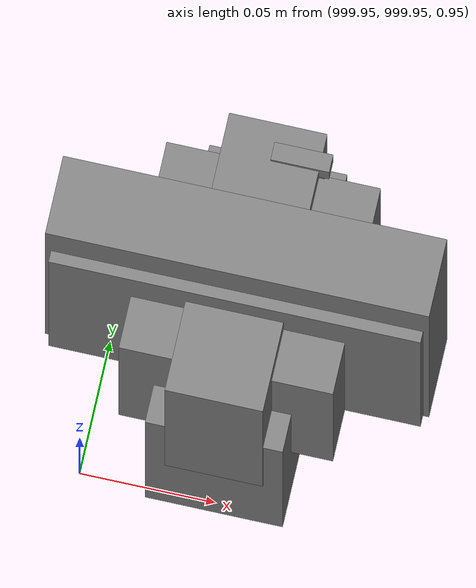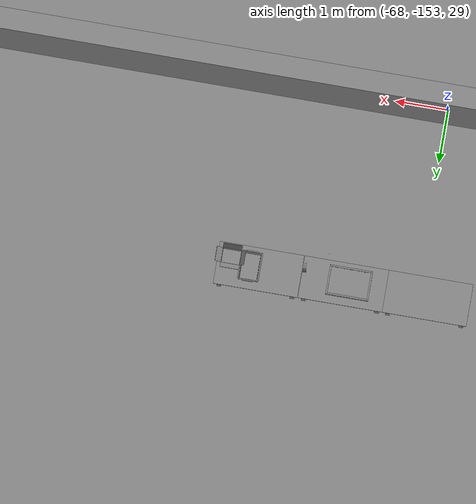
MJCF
<mujoco>
    <option gravity="0.000000000 0.000000000 -9.810000420" timestep="0.0049999999" integrator="implicitfast" density="1.225" viscosity="1.8000001e-05" noslip_iterations="10" iterations="100" sdf_iterations="50">
        <flag multiccd="disable"/>
    </option>
    <size memory="1000M"/>
    <compiler coordinate="local"/>
    <worldbody>
        <light cutoff="30" pos="0 1 1" dir="0 -1 -2"/>
        <light cutoff="30" pos="0 -1 1" dir="0 1 -2"/>
        <body pos="1000.000000000 1000.000000000 1.000000000" euler="0.000000000 0.000000000 180.000000000" name="openloong_gripper_2f85_fix_base_usda_battery_01">
            <geom contype="1" conaffinity="1" density="1000" type="box" material="" rgba="0.500000000 0.500000000 0.500000000 1.000000000" solimp="0.899999976 0.949999988 0.001000000" friction="1.000000000 0.005000000 0.000100000" solref="0.020000000 1.000000000" margin="0" condim="3" group="0" pos="-0.011123657 -0.041940309 0.101691343" quat="1.000000000 0.000000000 0.000000000 0.000000000" size="0.010800000 0.003375000 0.004725000" name="openloong_gripper_2f85_fix_base_usda_geom_4CF28AE4_62D4_461E_9969_51525B250413"/>
            <geom contype="1" conaffinity="1" density="1000" type="box" material="" rgba="0.500000000 0.500000000 0.500000000 1.000000000" solimp="0.899999976 0.949999988 0.001000000" friction="1.000000000 0.005000000 0.000100000" solref="0.020000000 1.000000000" margin="0" condim="3" group="0" pos="-0.010876465 -0.044247437 0.047066893" quat="0.998702705 -0.050920475 0.000000000 0.000000000" size="0.009450001 0.002700000 0.024975000" name="openloong_gripper_2f85_fix_base_usda_geom_AAC64D4C_55E5_42DE_B1E1_5D2BC521C062"/>
            <geom contype="1" conaffinity="1" density="1000" type="box" material="" rgba="0.500000000 0.500000000 0.500000000 1.000000000" solimp="0.899999976 0.949999988 0.001000000" friction="1.000000000 0.005000000 0.000100000" solref="0.020000000 1.000000000" margin="0" condim="3" group="0" pos="-0.001235962 -0.000659180 0.047381196" quat="1.000000000 0.000000000 0.000000000 0.000000000" size="0.039420001 0.039150000 0.047250003" name="openloong_gripper_2f85_fix_base_usda_geom_B7C69C05_3424_4B74_94DA_C5153FDAECDA"/>
            <geom contype="1" conaffinity="1" density="1000" type="box" material="" rgba="0.500000000 0.500000000 0.500000000 1.000000000" solimp="0.899999976 0.949999988 0.001000000" friction="1.000000000 0.005000000 0.000100000" solref="0.020000000 1.000000000" margin="0" condim="3" group="0" pos="-0.010876465 -0.039138794 0.009851727" quat="1.000000000 0.000000000 0.000000000 0.000000000" size="0.009450001 0.010800000 0.013500000" name="openloong_gripper_2f85_fix_base_usda_geom_D7FFDCC4_CC04_41CD_B0AF_72583BC50B3A"/>
            <geom contype="1" conaffinity="1" density="1000" type="box" material="" rgba="0.500000000 0.500000000 0.500000000 1.000000000" solimp="0.899999976 0.949999988 0.001000000" friction="1.000000000 0.005000000 0.000100000" solref="0.020000000 1.000000000" margin="0" condim="3" group="0" pos="-0.010876465 -0.041528322 0.071508206" quat="1.000000000 0.000000000 0.000000000 0.000000000" size="0.009450001 0.002700000 0.027000001" name="openloong_gripper_2f85_fix_base_usda_geom_5FC041E7_4B7D_48E6_B007_B4C8EADB7B40"/>
            <freejoint name="openloong_gripper_2f85_fix_base_usda_battery_01_joint"/>
            <site size="0.005000000 0.005000000 0.005000000" rgba="0.500000000 0.500000000 0.500000000 1.000000000" pos="0.000000000 0.000000000 0.000000000" quat="0.999961913 0.008726500 0.000000000 0.000000000" group="0" type="sphere" name="openloong_gripper_2f85_fix_base_usda_battery_01site"/>
        </body>
        <body pos="-65.846618652 -149.169631958 31.169528961" euler="27.298286438 75.907440186 -149.170272827" mocap="true" name="spotlight3_SpotLight"/>
        <body pos="1000.000000000 1000.000000000 1.000000000" euler="0.000000000 0.000000000 180.000000000" name="openloong_gripper_2f85_fix_base_usda_cpu_fan">
            <geom contype="1" conaffinity="1" density="1000" type="box" material="" rgba="0.500000000 0.500000000 0.500000000 1.000000000" solimp="0.899999976 0.949999988 0.001000000" friction="1.000000000 0.005000000 0.000100000" solref="0.020000000 1.000000000" margin="0" condim="3" group="0" pos="0.000000000 0.000000000 0.070034981" quat="0.000000000 0.000000000 0.000000000 1.000000000" size="0.070700005 0.014699999 0.070700005" name="openloong_gripper_2f85_fix_base_usda_geom_6D52F3C9_B402_4B6B_976E_E5540804FFA5"/>
            <freejoint name="openloong_gripper_2f85_fix_base_usda_cpu_fan_joint"/>
            <site size="0.005000000 0.005000000 0.005000000" rgba="0.500000000 0.500000000 0.500000000 1.000000000" pos="0.000000000 0.000000000 0.000000000" quat="0.999961913 0.008726535 0.000000000 0.000000000" group="0" type="sphere" name="openloong_gripper_2f85_fix_base_usda_cpu_fancsite"/>
        </body>
        <body pos="1000.000000000 1000.000000000 1.000000000" euler="0.000000000 0.000000000 180.000000000" name="openloong_gripper_2f85_fix_base_usda_wifi_box">
            <geom contype="1" conaffinity="1" density="1000" type="box" material="" rgba="0.500000000 0.500000000 0.500000000 1.000000000" solimp="0.899999976 0.949999988 0.001000000" friction="1.000000000 0.005000000 0.000100000" solref="0.020000000 1.000000000" margin="0" condim="3" group="0" pos="0.000000000 0.000000000 0.058978677" quat="0.000000000 0.000000047 0.000000000 1.000000000" size="0.068499997 0.018999999 0.059000000" name="openloong_gripper_2f85_fix_base_usda_geom_61FFB6AD_78AD_41DD_9ABD_A6BBDD69DABA"/>
            <freejoint name="openloong_gripper_2f85_fix_base_usda_wifi_box_joint"/>
            <site size="0.005000000 0.005000000 0.005000000" rgba="0.500000000 0.500000000 0.500000000 1.000000000" pos="0.000000000 0.000000000 0.000000000" quat="0.999961913 0.008726500 0.000000000 0.000000000" group="0" type="sphere" name="openloong_gripper_2f85_fix_base_usda_wifi_boxsite"/>
        </body>
        <body pos="-66.015289307 -149.159912109 31.167291641" euler="28.721620560 18.159507751 111.182899475" mocap="true" name="spotlight6_SpotLight"/>
        <body pos="1000.000000000 1000.000000000 1.000000000" euler="0.000011953 0.000005123 -179.999984741" name="openloong_gripper_2f85_fix_base_usda_intel_box">
            <geom contype="1" conaffinity="1" density="1000" type="box" material="" rgba="0.500000000 0.500000000 0.500000000 1.000000000" solimp="0.899999976 0.949999988 0.001000000" friction="1.000000000 0.005000000 0.000100000" solref="0.020000000 1.000000000" margin="0" condim="3" group="0" pos="0.000000000 -0.000067139 0.000082284" quat="0.707106709 0.000000225 0.000000253 0.707106650" size="0.052800003 0.025300000 0.052800003" name="openloong_gripper_2f85_fix_base_usda_geom_C2F74FE3_7694_4F09_833D_8C7BC093027B"/>
            <freejoint name="openloong_gripper_2f85_fix_base_usda_intel_box_joint"/>
            <site size="0.005000000 0.005000000 0.005000000" rgba="0.500000000 0.500000000 0.500000000 1.000000000" pos="0.000000000 0.000000000 0.000000000" quat="0.999961913 0.008726500 0.000000000 0.000000000" group="0" type="sphere" name="openloong_gripper_2f85_fix_base_usda_intel_boxsite"/>
        </body>
        <body pos="-66.289520264 -148.947769165 31.163724899" euler="-99.249748230 60.446918488 80.763359070" mocap="true" name="spotlight5_SpotLight"/>
        <body pos="1000.000000000 999.999938965 1.000000000" euler="0.000000000 0.000000000 180.000000000" name="openloong_gripper_2f85_fix_base_usda_intelcore_i5">
            <geom contype="1" conaffinity="1" density="1000" type="box" material="" rgba="0.500000000 0.500000000 0.500000000 1.000000000" solimp="0.899999976 0.949999988 0.001000000" friction="1.000000000 0.005000000 0.000100000" solref="0.020000000 1.000000000" margin="0" condim="3" group="0" pos="0.000000000 0.000000000 0.051722717" quat="0.707106709 0.000000000 0.000000000 -0.707106769" size="0.052800000 0.018080002 0.052800000" name="openloong_gripper_2f85_fix_base_usda_geom_6DBDCC65_4AFB_4A60_AC44_E30EB8F0F41C"/>
            <freejoint name="openloong_gripper_2f85_fix_base_usda_intelcore_i5_joint"/>
            <site size="0.005000000 0.005000000 0.005000000" rgba="0.500000000 0.500000000 0.500000000 1.000000000" pos="0.000000000 0.000000000 0.000000000" quat="0.999961913 0.008726534 0.000000000 0.000000000" group="0" type="sphere" name="openloong_gripper_2f85_fix_base_usda_intelcore_i5site"/>
        </body>
        <body pos="-64.866622925 -149.383972168 30.183746338" euler="89.999984741 89.999946594 0.000000000" name="openloong_gripper_2f85_fix_base_usda_bluebox_01">
            <geom contype="1" conaffinity="1" density="1000" type="box" material="" rgba="0.500000000 0.500000000 0.500000000 1.000000000" solimp="0.899999976 0.949999988 0.001000000" friction="1.000000000 0.005000000 0.000100000" solref="0.020000000 1.000000000" margin="0" condim="3" group="0" pos="0.276580811 0.187225342 0.000068665" quat="0.707106948 0.000077471 0.707106352 0.000077486" size="0.100000001 0.057999998 0.010000000" name="openloong_gripper_2f85_fix_base_usda_geom_3B2AE589_57C7_43BD_A546_E3A04AA24F26"/>
            <geom contype="1" conaffinity="1" density="1000" type="box" material="" rgba="0.500000000 0.500000000 0.500000000 1.000000000" solimp="0.899999976 0.949999988 0.001000000" friction="1.000000000 0.005000000 0.000100000" solref="0.020000000 1.000000000" margin="0" condim="3" group="0" pos="0.000000000 0.002883911 0.000000000" quat="0.999999881 0.000000000 0.000000000 0.000000000" size="0.254000008 0.003000000 0.172000006" name="openloong_gripper_2f85_fix_base_usda_geom_DEAFB518_2A98_4F52_83C0_A1060FADC1AD"/>
            <geom contype="1" conaffinity="1" density="1000" type="box" material="" rgba="0.500000000 0.500000000 0.500000000 1.000000000" solimp="0.899999976 0.949999988 0.001000000" friction="1.000000000 0.005000000 0.000100000" solref="0.020000000 1.000000000" margin="0" condim="3" group="0" pos="0.000000000 0.124874115 0.173484802" quat="0.999796331 0.020176515 -0.000000015 0.000000030" size="0.259999990 0.119999997 0.007000000" name="openloong_gripper_2f85_fix_base_usda_geom_D9C3EDB2_3731_4CA7_90A4_4BB6466E83FF"/>
            <geom contype="1" conaffinity="1" density="1000" type="box" material="" rgba="0.500000000 0.500000000 0.500000000 1.000000000" solimp="0.899999976 0.949999988 0.001000000" friction="1.000000000 0.005000000 0.000100000" solref="0.020000000 1.000000000" margin="0" condim="3" group="0" pos="0.000000000 0.124874115 -0.173469543" quat="0.999796331 -0.020176545 -0.000000015 0.000000000" size="0.259999990 0.119999997 0.007000000" name="openloong_gripper_2f85_fix_base_usda_geom_9F843237_143B_4C01_8F28_09583F838559"/>
            <geom contype="1" conaffinity="1" density="1000" type="box" material="" rgba="0.500000000 0.500000000 0.500000000 1.000000000" solimp="0.899999976 0.949999988 0.001000000" friction="1.000000000 0.005000000 0.000100000" solref="0.020000000 1.000000000" margin="0" condim="3" group="0" pos="0.000000000 0.214008331 0.188980103" quat="0.999912977 0.013176724 0.000000015 0.000000000" size="0.259999990 0.029999999 0.012500000" name="openloong_gripper_2f85_fix_base_usda_geom_9E089A89_5012_487C_AED1_A1CECAE7159F"/>
            <geom contype="1" conaffinity="1" density="1000" type="box" material="" rgba="0.500000000 0.500000000 0.500000000 1.000000000" solimp="0.899999976 0.949999988 0.001000000" friction="1.000000000 0.005000000 0.000100000" solref="0.020000000 1.000000000" margin="0" condim="3" group="0" pos="-0.258361816 0.125289917 0.001876831" quat="0.702796936 -0.020792112 0.710783124 0.020769298" size="0.189999998 0.119999997 0.009000000" name="openloong_gripper_2f85_fix_base_usda_geom_E3BB1B14_B45E_4B45_817D_D8B8456CA971"/>
            <geom contype="1" conaffinity="1" density="1000" type="box" material="" rgba="0.500000000 0.500000000 0.500000000 1.000000000" solimp="0.899999976 0.949999988 0.001000000" friction="1.000000000 0.005000000 0.000100000" solref="0.020000000 1.000000000" margin="0" condim="3" group="0" pos="0.000000000 0.214008331 -0.188980103" quat="0.999912977 -0.013176769 0.000000030 0.000000015" size="0.259999990 0.029999999 0.012500000" name="openloong_gripper_2f85_fix_base_usda_geom_F1B55C19_2E9D_4697_B39E_1F25E9057069"/>
            <geom contype="1" conaffinity="1" density="1000" type="box" material="" rgba="0.500000000 0.500000000 0.500000000 1.000000000" solimp="0.899999976 0.949999988 0.001000000" friction="1.000000000 0.005000000 0.000100000" solref="0.020000000 1.000000000" margin="0" condim="3" group="0" pos="-0.276611328 0.187225342 0.000068665" quat="0.707106650 0.000077441 0.707106709 0.000077456" size="0.100000001 0.057999998 0.010000000" name="openloong_gripper_2f85_fix_base_usda_geom_D1EBC614_29D1_497C_A6F8_978D3AB1BD1C"/>
            <geom contype="1" conaffinity="1" density="1000" type="box" material="" rgba="0.500000000 0.500000000 0.500000000 1.000000000" solimp="0.899999976 0.949999988 0.001000000" friction="1.000000000 0.005000000 0.000100000" solref="0.020000000 1.000000000" margin="0" condim="3" group="0" pos="0.258331299 0.125289917 0.001876831" quat="0.702851415 0.018856421 0.710823774 -0.019329369" size="0.189999998 0.119999997 0.009000000" name="openloong_gripper_2f85_fix_base_usda_geom_90C28C9A_0953_4E56_84D4_42EF07313192"/>
            <freejoint name="openloong_gripper_2f85_fix_base_usda_bluebox_01_joint"/>
            <site size="0.005000000 0.005000000 0.005000000" rgba="0.500000000 0.500000000 0.500000000 1.000000000" pos="0.000000000 0.000000000 0.000000000" quat="0.999961913 0.008726534 0.000000000 0.000000000" group="0" type="sphere" name="openloong_gripper_2f85_fix_base_usda_bluebox_01site"/>
        </body>
        <body pos="-64.496299744 -149.491867065 30.235729218" euler="0.000000000 0.000000000 89.999946594" name="openloong_gripper_2f85_fix_base_usda_cardboardbox_01">
            <geom contype="1" conaffinity="1" density="1000" type="box" material="" rgba="0.500000000 0.500000000 0.500000000 1.000000000" solimp="0.899999976 0.949999988 0.001000000" friction="1.000000000 0.005000000 0.000100000" solref="0.020000000 1.000000000" margin="0" condim="3" group="0" pos="-0.003166199 -0.004086494 0.005052090" quat="1.000000000 0.000000000 0.000000000 0.000000000" size="0.142499998 0.177500010 0.005000000" name="openloong_gripper_2f85_fix_base_usda_geom_461ED2D9_381C_411B_BAB4_EB14971BAED3"/>
            <geom contype="1" conaffinity="1" density="1000" type="box" material="" rgba="0.500000000 0.500000000 0.500000000 1.000000000" solimp="0.899999976 0.949999988 0.001000000" friction="1.000000000 0.005000000 0.000100000" solref="0.020000000 1.000000000" margin="0" condim="3" group="0" pos="-0.003166199 0.170316696 0.150570869" quat="1.000000000 0.000000000 0.000000000 0.000000000" size="0.142499998 0.005000000 0.149999991" name="openloong_gripper_2f85_fix_base_usda_geom_ADE6BEC0_2B3B_4E22_B868_818BF37853F2"/>
            <geom contype="1" conaffinity="1" density="1000" type="box" material="" rgba="0.500000000 0.500000000 0.500000000 1.000000000" solimp="0.899999976 0.949999988 0.001000000" friction="1.000000000 0.005000000 0.000100000" solref="0.020000000 1.000000000" margin="0" condim="3" group="0" pos="-0.147399902 -0.005307198 0.150570869" quat="1.000000000 0.000000000 0.000000000 0.000000000" size="0.005000000 0.177500010 0.149999991" name="openloong_gripper_2f85_fix_base_usda_geom_7A7CB837_F1EE_4407_B4C1_BE1171D178E4"/>
            <geom contype="1" conaffinity="1" density="1000" type="box" material="" rgba="0.500000000 0.500000000 0.500000000 1.000000000" solimp="0.899999976 0.949999988 0.001000000" friction="1.000000000 0.005000000 0.000100000" solref="0.020000000 1.000000000" margin="0" condim="3" group="0" pos="0.140275955 -0.005307198 0.150570869" quat="1.000000000 0.000000000 0.000000000 0.000000000" size="0.005000000 0.177500010 0.149999991" name="openloong_gripper_2f85_fix_base_usda_geom_35962B3C_74C4_401E_A5ED_4FB1182668D5"/>
            <geom contype="1" conaffinity="1" density="1000" type="box" material="" rgba="0.500000000 0.500000000 0.500000000 1.000000000" solimp="0.899999976 0.949999988 0.001000000" friction="1.000000000 0.005000000 0.000100000" solref="0.020000000 1.000000000" margin="0" condim="3" group="0" pos="-0.003166199 -0.181550980 0.150570869" quat="1.000000000 0.000000000 0.000000000 0.000000000" size="0.142499998 0.005000000 0.149999991" name="openloong_gripper_2f85_fix_base_usda_geom_667EAA1E_35E2_435E_BB88_4E679620CDFD"/>
            <freejoint name="openloong_gripper_2f85_fix_base_usda_cardboardbox_01_joint"/>
            <site size="0.005000000 0.005000000 0.005000000" rgba="0.500000000 0.500000000 0.500000000 1.000000000" pos="0.000000000 0.000000000 0.000000000" quat="0.999961913 0.008726535 0.000000000 0.000000000" group="0" type="sphere" name="openloong_gripper_2f85_fix_base_usda_site_C571BF89_1AC5_4680_8F0F_2331EEA185D1"/>
            <body pos="0.139160156 -0.004048347 0.301930904" euler="-179.999954224 49.383502960 179.999954224" name="openloong_gripper_2f85_fix_base_usda_A1_006">
                <geom contype="1" conaffinity="1" density="1000" type="box" material="" rgba="0.500000000 0.500000000 0.500000000 1.000000000" solimp="0.899999976 0.949999988 0.001000000" friction="1.000000000 0.005000000 0.000100000" solref="0.020000000 1.000000000" margin="0" condim="3" group="0" pos="-0.071587563 0.000009537 0.001745224" quat="0.999999881 0.000000000 0.000000000 0.000000000" size="0.071249999 0.179999992 0.002500000" name="openloong_gripper_2f85_fix_base_usda_geom_DACC4365_3629_4EA6_87C9_8B68A41B4E35"/>
                <joint armature="0" stiffness="0.07" damping="0.0099999998" axis="0.000000 1.000000 0.000000" type="hinge" name="openloong_gripper_2f85_fix_base_usda_A1_006"/>
            </body>
            <body pos="-0.145902634 -0.004086494 0.301938057" euler="-180.000000000 -60.000011444 -180.000000000" name="openloong_gripper_2f85_fix_base_usda_A2_006">
                <geom contype="1" conaffinity="1" density="1000" type="box" material="" rgba="0.500000000 0.500000000 0.500000000 1.000000000" solimp="0.899999976 0.949999988 0.001000000" friction="1.000000000 0.005000000 0.000100000" solref="0.020000000 1.000000000" margin="0" condim="3" group="0" pos="0.071268082 0.000009537 0.002717972" quat="0.000002921 0.000000000 -0.000000030 0.999999881" size="0.071249999 0.179999992 0.002500000" name="openloong_gripper_2f85_fix_base_usda_geom_1298FCE0_6DDB_4C6F_BC97_E09C5153E58A"/>
                <joint armature="0" stiffness="0.07" damping="0.0099999998" axis="0.000000 1.000000 0.000000" type="hinge" name="openloong_gripper_2f85_fix_base_usda_A2_006"/>
            </body>
            <body pos="-0.003385544 0.175991058 0.301930904" euler="-125.858116150 -0.000004561 0.000002331" name="openloong_gripper_2f85_fix_base_usda_B2_006">
                <geom contype="1" conaffinity="1" density="1000" type="box" material="" rgba="0.500000000 0.500000000 0.500000000 1.000000000" solimp="0.899999976 0.949999988 0.001000000" friction="1.000000000 0.005000000 0.000100000" solref="0.020000000 1.000000000" margin="0" condim="3" group="0" pos="0.000009537 -0.070939064 -0.002470016" quat="0.999614120 0.027776197 -0.000000015 0.000000030" size="0.137500003 0.064999998 0.005000000" name="openloong_gripper_2f85_fix_base_usda_geom_EC6F8A60_CBA4_43D4_BE9D_CEA21A79F168"/>
                <joint armature="0" stiffness="0.07" damping="0.0099999998" axis="1.000000 0.000000 0.000000" type="hinge" name="openloong_gripper_2f85_fix_base_usda_B2_006"/>
            </body>
            <body pos="-0.003385544 -0.184140205 0.301938057" euler="147.805557251 0.000000000 0.000000000" name="openloong_gripper_2f85_fix_base_usda_B1_006">
                <geom contype="1" conaffinity="1" density="1000" type="box" material="" rgba="0.500000000 0.500000000 0.500000000 1.000000000" solimp="0.899999976 0.949999988 0.001000000" friction="1.000000000 0.005000000 0.000100000" solref="0.020000000 1.000000000" margin="0" condim="3" group="0" pos="-0.000028610 0.070202351 -0.002703667" quat="0.999614179 -0.027776167 0.000000000 0.000000000" size="0.137500003 0.064999998 0.005000000" name="openloong_gripper_2f85_fix_base_usda_geom_9167A631_EDB7_44BE_AB4C_5666245114AD"/>
                <joint armature="0" stiffness="0.07" damping="0.0099999998" axis="1.000000 0.000000 0.000000" type="hinge" name="openloong_gripper_2f85_fix_base_usda_B1_006"/>
            </body>
        </body>
        <body pos="-65.882858276 -149.481979370 30.229999542" euler="-64.487716675 0.000000000 0.000000000" name="openloong_gripper_2f85_fix_base_usda_Barcode">
            <geom contype="1" conaffinity="1" density="1000" type="box" material="" rgba="0.500000000 0.500000000 0.500000000 1.000000000" solimp="0.899999976 0.949999988 0.001000000" friction="1.000000000 0.005000000 0.000100000" solref="0.020000000 1.000000000" margin="0" condim="3" group="0" pos="0.000000000 0.013038635 0.001419067" quat="0.000000000 0.000000000 0.000000000 1.000000119" size="0.034000002 0.010000000 0.017999999" name="openloong_gripper_2f85_fix_base_usda_geom_905FB125_4004_4611_8BB1_24F003D539C5"/>
            <geom contype="1" conaffinity="1" density="1000" type="box" material="" rgba="0.500000000 0.500000000 0.500000000 1.000000000" solimp="0.899999976 0.949999988 0.001000000" friction="1.000000000 0.005000000 0.000100000" solref="0.020000000 1.000000000" margin="0" condim="3" group="0" pos="0.000000000 -0.035301208 -0.007095337" quat="0.000000000 0.000000000 -0.043619365 0.999048233" size="0.028999999 0.010000000 0.020000000" name="openloong_gripper_2f85_fix_base_usda_geom_2B7D2AC3_F6A2_48E5_A7C0_A0FD41EA3B5D"/>
            <geom contype="1" conaffinity="1" density="1000" type="box" material="" rgba="0.500000000 0.500000000 0.500000000 1.000000000" solimp="0.899999976 0.949999988 0.001000000" friction="1.000000000 0.005000000 0.000100000" solref="0.020000000 1.000000000" margin="0" condim="3" group="0" pos="0.000000000 -0.043411255 -0.011749268" quat="0.922262907 0.386563420 0.000000000 0.000000000" size="0.026000001 0.010000000 0.020000000" name="openloong_gripper_2f85_fix_base_usda_geom_729FFFB1_EF67_4CFA_BD3A_8477AF09BEB3"/>
            <geom contype="1" conaffinity="1" density="1000" type="box" material="" rgba="0.500000000 0.500000000 0.500000000 1.000000000" solimp="0.899999976 0.949999988 0.001000000" friction="1.000000000 0.005000000 0.000100000" solref="0.020000000 1.000000000" margin="0" condim="3" group="0" pos="0.000000000 -0.016967773 -0.031860352" quat="0.000000000 0.000000000 0.000000000 1.000000119" size="0.008000000 0.010000000 0.013000000" name="openloong_gripper_2f85_fix_base_usda_geom_E76D3FCB_216A_47A2_A465_3AFA62F1CE74"/>
            <geom contype="1" conaffinity="1" density="1000" type="box" material="" rgba="0.500000000 0.500000000 0.500000000 1.000000000" solimp="0.899999976 0.949999988 0.001000000" friction="1.000000000 0.005000000 0.000100000" solref="0.020000000 1.000000000" margin="0" condim="3" group="0" pos="0.000000000 -0.001869202 0.000312805" quat="0.953716993 0.300705761 0.000000000 0.000000000" size="0.032000002 0.010000000 0.018999999" name="openloong_gripper_2f85_fix_base_usda_geom_01D83466_B7D3_403C_AB7D_DA49654A9600"/>
            <geom contype="1" conaffinity="1" density="1000" type="box" material="" rgba="0.500000000 0.500000000 0.500000000 1.000000000" solimp="0.899999976 0.949999988 0.001000000" friction="1.000000000 0.005000000 0.000100000" solref="0.020000000 1.000000000" margin="0" condim="3" group="0" pos="0.000000000 -0.019531250 -0.003173828" quat="0.953716993 0.300705761 0.000000000 0.000000000" size="0.030999999 0.010000000 0.020000000" name="openloong_gripper_2f85_fix_base_usda_geom_24033FE7_966A_414D_B2CC_1609CE448749"/>
            <geom contype="1" conaffinity="1" density="1000" type="box" material="" rgba="0.500000000 0.500000000 0.500000000 1.000000000" solimp="0.899999976 0.949999988 0.001000000" friction="1.000000000 0.005000000 0.000100000" solref="0.020000000 1.000000000" margin="0" condim="3" group="0" pos="0.000000000 -0.035301208 -0.007095337" quat="0.953716993 0.300705761 0.000000000 0.000000000" size="0.028999999 0.010000000 0.020000000" name="openloong_gripper_2f85_fix_base_usda_geom_73EDB81D_7CE0_4DBD_9A83_3C44ADD1D439"/>
            <geom contype="1" conaffinity="1" density="1000" type="box" material="" rgba="0.500000000 0.500000000 0.500000000 1.000000000" solimp="0.899999976 0.949999988 0.001000000" friction="1.000000000 0.005000000 0.000100000" solref="0.020000000 1.000000000" margin="0" condim="3" group="0" pos="0.000000000 -0.042617798 -0.071121216" quat="0.000000000 0.000000000 0.000000000 1.000000119" size="0.013000000 0.021000000 0.059999999" name="openloong_gripper_2f85_fix_base_usda_geom_9C0951B3_0086_40F3_A15E_A170F96DE905"/>
            <freejoint name="openloong_gripper_2f85_fix_base_usda_Barcode_joint"/>
            <site size="0.005000000 0.005000000 0.005000000" rgba="0.500000000 0.500000000 0.500000000 1.000000000" pos="0.000000000 0.000000000 0.000000000" quat="1.000000000 0.000000000 0.000000000 0.000000000" group="0" type="sphere" name="openloong_gripper_2f85_fix_base_usda_Barcode_site"/>
        </body>
        <body pos="-66.745018005 -149.392349243 30.184000015" euler="0.000000000 0.000000000 89.999946594" name="[22330784456883]_Basket_01">
            <geom contype="1" conaffinity="1" density="1000" type="box" material="" rgba="0.500000000 0.500000000 0.500000000 1.000000000" solimp="0.899999976 0.949999988 0.001000000" friction="1.000000000 0.005000000 0.000100000" solref="0.020000000 1.000000000" margin="0" condim="3" group="0" pos="-0.052425385 0.389207840 0.089787483" quat="0.707107008 0.000000000 0.000000000 0.707106411" size="0.014249999 0.014249999 0.059999999" name="[22330784456883]_geom_6E2C76F2_A69E_4DA3_8467_B345B1C680CB"/>
            <geom contype="1" conaffinity="1" density="1000" type="box" material="" rgba="0.500000000 0.500000000 0.500000000 1.000000000" solimp="0.899999976 0.949999988 0.001000000" friction="1.000000000 0.005000000 0.000100000" solref="0.020000000 1.000000000" margin="0" condim="3" group="0" pos="0.264015198 -0.133043289 0.089787483" quat="0.707107008 0.000000000 0.000000000 0.707106411" size="0.014249999 0.014249999 0.059999999" name="[22330784456883]_geom_3EBB9302_380E_424C_9C98_8FA2C1053F3D"/>
            <geom contype="1" conaffinity="1" density="1000" type="box" material="" rgba="0.500000000 0.500000000 0.500000000 1.000000000" solimp="0.899999976 0.949999988 0.001000000" friction="1.000000000 0.005000000 0.000100000" solref="0.020000000 1.000000000" margin="0" condim="3" group="0" pos="-0.264015198 -0.265548706 0.089793205" quat="0.707107008 0.000000000 0.000000000 0.707106411" size="0.014249999 0.014249999 0.059999999" name="[22330784456883]_geom_B39845E3_DBD7_4323_B8AD_743ED454591A"/>
            <geom contype="1" conaffinity="1" density="1000" type="box" material="" rgba="0.500000000 0.500000000 0.500000000 1.000000000" solimp="0.899999976 0.949999988 0.001000000" friction="1.000000000 0.005000000 0.000100000" solref="0.020000000 1.000000000" margin="0" condim="3" group="0" pos="-0.160263062 -0.389322281 0.089793205" quat="0.707107008 0.000000000 0.000000000 0.707106411" size="0.014249999 0.014249999 0.059999999" name="[22330784456883]_geom_BE695168_9FA4_45A0_8A9B_3449E2B0EC97"/>
            <geom contype="1" conaffinity="1" density="1000" type="box" material="" rgba="0.500000000 0.500000000 0.500000000 1.000000000" solimp="0.899999976 0.949999988 0.001000000" friction="1.000000000 0.005000000 0.000100000" solref="0.020000000 1.000000000" margin="0" condim="3" group="0" pos="0.162265778 -0.389322281 0.089787483" quat="0.707107008 0.000000000 0.000000000 0.707106411" size="0.014249999 0.014249999 0.059999999" name="[22330784456883]_geom_D3684F40_3966_4F38_A6CB_38F959F2E808"/>
            <geom contype="1" conaffinity="1" density="1000" type="box" material="" rgba="0.500000000 0.500000000 0.500000000 1.000000000" solimp="0.899999976 0.949999988 0.001000000" friction="1.000000000 0.005000000 0.000100000" solref="0.020000000 1.000000000" margin="0" condim="3" group="0" pos="0.264015198 0.389207840 0.089787483" quat="0.707107008 0.000000000 0.000000000 0.707106411" size="0.014249999 0.014249999 0.059999999" name="[22330784456883]_geom_6229E0B2_1175_4B16_A147_4CE552ECF25D"/>
            <geom contype="1" conaffinity="1" density="1000" type="box" material="" rgba="0.500000000 0.500000000 0.500000000 1.000000000" solimp="0.899999976 0.949999988 0.001000000" friction="1.000000000 0.005000000 0.000100000" solref="0.020000000 1.000000000" margin="0" condim="3" group="0" pos="-0.264015198 -0.133043289 0.089793205" quat="0.707107008 0.000000000 0.000000000 0.707106411" size="0.014249999 0.014249999 0.059999999" name="[22330784456883]_geom_106EB0DB_4082_4E2A_9570_10214DA50293"/>
            <geom contype="1" conaffinity="1" density="1000" type="box" material="" rgba="0.500000000 0.500000000 0.500000000 1.000000000" solimp="0.899999976 0.949999988 0.001000000" friction="1.000000000 0.005000000 0.000100000" solref="0.020000000 1.000000000" margin="0" condim="3" group="0" pos="-0.264026642 0.269256592 0.089793205" quat="0.707107008 0.000000000 0.000000000 0.707106411" size="0.014249999 0.014249999 0.059999999" name="[22330784456883]_geom_85C01DD1_B4C0_4729_9D6E_AED852B082BD"/>
            <geom contype="1" conaffinity="1" density="1000" type="box" material="" rgba="0.500000000 0.500000000 0.500000000 1.000000000" solimp="0.899999976 0.949999988 0.001000000" friction="1.000000000 0.005000000 0.000100000" solref="0.020000000 1.000000000" margin="0" condim="3" group="0" pos="0.054462433 0.389207840 0.089787483" quat="0.707107008 0.000000000 0.000000000 0.707106411" size="0.014249999 0.014249999 0.059999999" name="[22330784456883]_geom_67BF49F6_7AC2_4FFF_9A1B_9B90BF20351A"/>
            <geom contype="1" conaffinity="1" density="1000" type="box" material="" rgba="0.500000000 0.500000000 0.500000000 1.000000000" solimp="0.899999976 0.949999988 0.001000000" friction="1.000000000 0.005000000 0.000100000" solref="0.020000000 1.000000000" margin="0" condim="3" group="0" pos="0.054462433 -0.389322281 0.089787483" quat="0.707107008 0.000000000 0.000000000 0.707106411" size="0.014249999 0.014249999 0.059999999" name="[22330784456883]_geom_D333D0A3_FBF7_4B86_AE3E_C61A430883CC"/>
            <geom contype="1" conaffinity="1" density="1000" type="box" material="" rgba="0.500000000 0.500000000 0.500000000 1.000000000" solimp="0.899999976 0.949999988 0.001000000" friction="1.000000000 0.005000000 0.000100000" solref="0.020000000 1.000000000" margin="0" condim="3" group="0" pos="0.264015198 0.269256592 0.089793205" quat="0.707107008 0.000000000 0.000000000 0.707106411" size="0.014249999 0.014249999 0.059999999" name="[22330784456883]_geom_0561ABA6_213F_44D2_B1CC_D317FDAC3BAE"/>
            <geom contype="1" conaffinity="1" density="1000" type="box" material="" rgba="0.500000000 0.500000000 0.500000000 1.000000000" solimp="0.899999976 0.949999988 0.001000000" friction="1.000000000 0.005000000 0.000100000" solref="0.020000000 1.000000000" margin="0" condim="3" group="0" pos="0.264015198 -0.389322281 0.089787483" quat="0.707107008 0.000000000 0.000000000 0.707106411" size="0.014249999 0.014249999 0.059999999" name="[22330784456883]_geom_A5787EF4_671C_4CED_A1BA_380AB65DA3CF"/>
            <geom contype="1" conaffinity="1" density="1000" type="box" material="" rgba="0.500000000 0.500000000 0.500000000 1.000000000" solimp="0.899999976 0.949999988 0.001000000" friction="1.000000000 0.005000000 0.000100000" solref="0.020000000 1.000000000" margin="0" condim="3" group="0" pos="0.000000000 0.000000000 0.015998840" quat="0.707107008 0.000000000 0.000000000 0.707106411" size="0.403499991 0.279000014 0.015750000" name="[22330784456883]_geom_89C3D01F_05FB_4AC1_BD02_FEC4AFCFFBCF"/>
            <geom contype="1" conaffinity="1" density="1000" type="box" material="" rgba="0.500000000 0.500000000 0.500000000 1.000000000" solimp="0.899999976 0.949999988 0.001000000" friction="1.000000000 0.005000000 0.000100000" solref="0.020000000 1.000000000" margin="0" condim="3" group="0" pos="0.000000000 -0.389476776 0.163619041" quat="0.707107008 0.000000000 0.000000000 0.707106411" size="0.015000000 0.277500004 0.015750000" name="[22330784456883]_geom_C8254FCB_C28D_421A_A415_5D8E473BE754"/>
            <geom contype="1" conaffinity="1" density="1000" type="box" material="" rgba="0.500000000 0.500000000 0.500000000 1.000000000" solimp="0.899999976 0.949999988 0.001000000" friction="1.000000000 0.005000000 0.000100000" solref="0.020000000 1.000000000" margin="0" condim="3" group="0" pos="0.162265778 0.389207840 0.089787483" quat="0.707107008 0.000000000 0.000000000 0.707106411" size="0.014249999 0.014249999 0.059999999" name="[22330784456883]_geom_E431DAD1_EBC0_46D1_8CC4_B8AEC67BACF7"/>
            <geom contype="1" conaffinity="1" density="1000" type="box" material="" rgba="0.500000000 0.500000000 0.500000000 1.000000000" solimp="0.899999976 0.949999988 0.001000000" friction="1.000000000 0.005000000 0.000100000" solref="0.020000000 1.000000000" margin="0" condim="3" group="0" pos="0.000000000 0.389471054 0.163619041" quat="0.707107008 0.000000000 0.000000000 0.707106411" size="0.015000000 0.277500004 0.015750000" name="[22330784456883]_geom_A7D8812D_9B21_450E_8E24_FDEDA3D6B4C7"/>
            <geom contype="1" conaffinity="1" density="1000" type="box" material="" rgba="0.500000000 0.500000000 0.500000000 1.000000000" solimp="0.899999976 0.949999988 0.001000000" friction="1.000000000 0.005000000 0.000100000" solref="0.020000000 1.000000000" margin="0" condim="3" group="0" pos="-0.263511658 0.000000000 0.163619041" quat="0.707107008 0.000000000 0.000000000 0.707106411" size="0.403499991 0.015000000 0.015750000" name="[22330784456883]_geom_A9DDA82C_2DBD_4725_A788_CAA4C652D85C"/>
            <geom contype="1" conaffinity="1" density="1000" type="box" material="" rgba="0.500000000 0.500000000 0.500000000 1.000000000" solimp="0.899999976 0.949999988 0.001000000" friction="1.000000000 0.005000000 0.000100000" solref="0.020000000 1.000000000" margin="0" condim="3" group="0" pos="-0.264015198 0.141334534 0.089793205" quat="0.707107008 0.000000000 0.000000000 0.707106411" size="0.014249999 0.014249999 0.059999999" name="[22330784456883]_geom_8D5030F9_1978_499D_AE39_8E4DB63C2204"/>
            <geom contype="1" conaffinity="1" density="1000" type="box" material="" rgba="0.500000000 0.500000000 0.500000000 1.000000000" solimp="0.899999976 0.949999988 0.001000000" friction="1.000000000 0.005000000 0.000100000" solref="0.020000000 1.000000000" margin="0" condim="3" group="0" pos="0.264015198 -0.265548706 0.089787483" quat="0.707107008 0.000000000 0.000000000 0.707106411" size="0.014249999 0.014249999 0.059999999" name="[22330784456883]_geom_4FF6CE70_7946_49DD_8002_F5DBA7E986DF"/>
            <geom contype="1" conaffinity="1" density="1000" type="box" material="" rgba="0.500000000 0.500000000 0.500000000 1.000000000" solimp="0.899999976 0.949999988 0.001000000" friction="1.000000000 0.005000000 0.000100000" solref="0.020000000 1.000000000" margin="0" condim="3" group="0" pos="-0.160263062 0.389207840 0.089787483" quat="0.707107008 0.000000000 0.000000000 0.707106411" size="0.014249999 0.014249999 0.059999999" name="[22330784456883]_geom_129D8C6D_825E_4C61_9AAB_3AA83F95AD0F"/>
            <geom contype="1" conaffinity="1" density="1000" type="box" material="" rgba="0.500000000 0.500000000 0.500000000 1.000000000" solimp="0.899999976 0.949999988 0.001000000" friction="1.000000000 0.005000000 0.000100000" solref="0.020000000 1.000000000" margin="0" condim="3" group="0" pos="-0.052425385 -0.389322281 0.089787483" quat="0.707107008 0.000000000 0.000000000 0.707106411" size="0.014249999 0.014249999 0.059999999" name="[22330784456883]_geom_36F6F255_B68D_4A1F_B943_2B9D656336CF"/>
            <geom contype="1" conaffinity="1" density="1000" type="box" material="" rgba="0.500000000 0.500000000 0.500000000 1.000000000" solimp="0.899999976 0.949999988 0.001000000" friction="1.000000000 0.005000000 0.000100000" solref="0.020000000 1.000000000" margin="0" condim="3" group="0" pos="-0.264026642 -0.389322281 0.089793205" quat="0.707107008 0.000000000 0.000000000 0.707106411" size="0.014249999 0.014249999 0.059999999" name="[22330784456883]_geom_0F9A839F_F40D_44E9_AC86_574B474C165F"/>
            <geom contype="1" conaffinity="1" density="1000" type="box" material="" rgba="0.500000000 0.500000000 0.500000000 1.000000000" solimp="0.899999976 0.949999988 0.001000000" friction="1.000000000 0.005000000 0.000100000" solref="0.020000000 1.000000000" margin="0" condim="3" group="0" pos="0.264015198 0.141334534 0.089787483" quat="0.707107008 0.000000000 0.000000000 0.707106411" size="0.014249999 0.014249999 0.059999999" name="[22330784456883]_geom_3B758474_C742_4782_92F4_15B61F39FF60"/>
            <geom contype="1" conaffinity="1" density="1000" type="box" material="" rgba="0.500000000 0.500000000 0.500000000 1.000000000" solimp="0.899999976 0.949999988 0.001000000" friction="1.000000000 0.005000000 0.000100000" solref="0.020000000 1.000000000" margin="0" condim="3" group="0" pos="-0.264015198 0.389207840 0.089793205" quat="0.707107008 0.000000000 0.000000000 0.707106411" size="0.014249999 0.014249999 0.059999999" name="[22330784456883]_geom_92B40C48_DD72_486D_A742_503219EC8899"/>
            <geom contype="1" conaffinity="1" density="1000" type="box" material="" rgba="0.500000000 0.500000000 0.500000000 1.000000000" solimp="0.899999976 0.949999988 0.001000000" friction="1.000000000 0.005000000 0.000100000" solref="0.020000000 1.000000000" margin="0" condim="3" group="0" pos="0.264015198 0.004480362 0.089787483" quat="0.707107008 0.000000000 0.000000000 0.707106411" size="0.014249999 0.014249999 0.059999999" name="[22330784456883]_geom_6B4597DE_612D_4DC0_AC74_651C4BA353D4"/>
            <geom contype="1" conaffinity="1" density="1000" type="box" material="" rgba="0.500000000 0.500000000 0.500000000 1.000000000" solimp="0.899999976 0.949999988 0.001000000" friction="1.000000000 0.005000000 0.000100000" solref="0.020000000 1.000000000" margin="0" condim="3" group="0" pos="0.263694763 -0.000011444 0.163619041" quat="0.707107008 0.000000000 0.000000000 0.707106411" size="0.403499991 0.015000000 0.015750000" name="[22330784456883]_geom_0CEF40D8_F96A_4F51_8374_CE0BF4919F6D"/>
            <geom contype="1" conaffinity="1" density="1000" type="box" material="" rgba="0.500000000 0.500000000 0.500000000 1.000000000" solimp="0.899999976 0.949999988 0.001000000" friction="1.000000000 0.005000000 0.000100000" solref="0.020000000 1.000000000" margin="0" condim="3" group="0" pos="-0.264015198 0.004480362 0.089793205" quat="0.707107008 0.000000000 0.000000000 0.707106411" size="0.014249999 0.014249999 0.059999999" name="[22330784456883]_geom_C6CF926D_AB08_44BD_8B35_5727E88B2ECB"/>
            <freejoint name="[22330784456883]_joint_9754D561_B96B_4519_9E32_0A6661D2A368"/>
        </body>
        <body pos="0.000000000 0.000000000 0.000000000" euler="0.000000000 0.000000000 0.000000000" name="Static Objects_Static Objects">
            <geom contype="1" conaffinity="1" density="1000" type="box" material="" rgba="0.500000000 0.500000000 0.500000000 1.000000000" solimp="0.899999976 0.949999988 0.001000000" friction="1.000000000 0.005000000 0.000100000" solref="0.020000000 1.000000000" margin="0" condim="3" group="0" pos="-67.544113159 -149.365814209 29.727830887" quat="0.500000417 0.499999970 0.499999553 0.499999970" size="0.381000012 0.319999993 0.041000001" name="Static Objects_geom_681E64DE_5C45_40EB_B543_0527E2F3F867"/>
            <geom contype="1" conaffinity="1" density="1000" type="box" material="" rgba="0.500000000 0.500000000 0.500000000 1.000000000" solimp="0.899999976 0.949999988 0.001000000" friction="1.000000000 0.005000000 0.000100000" solref="0.020000000 1.000000000" margin="0" condim="3" group="0" pos="-68.239501953 -149.365814209 30.086868286" quat="0.500000417 0.499999970 0.499999553 0.499999970" size="0.370999992 0.039500002 0.745000005" name="Static Objects_geom_3A907DEB_A757_4C56_ADFA_55EAA301ADCC"/>
            <geom contype="1" conaffinity="1" density="1000" type="box" material="" rgba="0.500000000 0.500000000 0.500000000 1.000000000" solimp="0.899999976 0.949999988 0.001000000" friction="1.000000000 0.005000000 0.000100000" solref="0.020000000 1.000000000" margin="0" condim="3" group="0" pos="-68.239501953 -149.365814209 30.147235870" quat="0.500000417 0.499999970 0.499999553 0.499999970" size="0.400000006 0.022000000 0.800000012" name="Static Objects_geom_790B78E9_3D80_48FE_AB70_54E0682ABC44"/>
            <geom contype="1" conaffinity="1" density="1000" type="box" material="" rgba="0.500000000 0.500000000 0.500000000 1.000000000" solimp="0.899999976 0.949999988 0.001000000" friction="1.000000000 0.005000000 0.000100000" solref="0.020000000 1.000000000" margin="0" condim="3" group="0" pos="-68.934890747 -149.365814209 29.727830887" quat="0.500000417 0.499999970 0.499999553 0.499999970" size="0.381000012 0.319999993 0.041000001" name="Static Objects_geom_7060787D_DBD2_49AB_8395_716DACF17EB2"/>
            <geom contype="1" conaffinity="1" density="1000" type="box" material="" rgba="0.500000000 0.500000000 0.500000000 1.000000000" solimp="0.899999976 0.949999988 0.001000000" friction="1.000000000 0.005000000 0.000100000" solref="0.020000000 1.000000000" margin="0" condim="3" group="0" pos="-68.239501953 -149.365814209 29.561563492" quat="0.500000417 0.499999970 0.499999553 0.499999970" size="0.020000000 0.022000000 0.660000026" name="Static Objects_geom_9B46C69F_17EE_4160_863D_2F7E9A8B6559"/>
            <geom contype="1" conaffinity="1" density="1000" type="box" material="" rgba="0.500000000 0.500000000 0.500000000 1.000000000" solimp="0.899999976 0.949999988 0.001000000" friction="1.000000000 0.005000000 0.000100000" solref="0.020000000 1.000000000" margin="0" condim="3" group="0" pos="-65.945671082 -149.365814209 29.727830887" quat="0.500000417 0.499999970 0.499999553 0.499999970" size="0.381000012 0.319999993 0.041000001" name="Static Objects_geom_2521A9EB_8BEA_413C_A3CC_1F86A2D0C281"/>
            <geom contype="1" conaffinity="1" density="1000" type="box" material="" rgba="0.500000000 0.500000000 0.500000000 1.000000000" solimp="0.899999976 0.949999988 0.001000000" friction="1.000000000 0.005000000 0.000100000" solref="0.020000000 1.000000000" margin="0" condim="3" group="0" pos="-66.641059875 -149.365814209 30.086868286" quat="0.500000417 0.499999970 0.499999553 0.499999970" size="0.370999992 0.039500002 0.745000005" name="Static Objects_geom_F5AB7D0A_F227_493D_97AA_D5D98711E9DF"/>
            <geom contype="1" conaffinity="1" density="1000" type="box" material="" rgba="0.500000000 0.500000000 0.500000000 1.000000000" solimp="0.899999976 0.949999988 0.001000000" friction="1.000000000 0.005000000 0.000100000" solref="0.020000000 1.000000000" margin="0" condim="3" group="0" pos="-66.641059875 -149.365814209 30.147235870" quat="0.500000417 0.499999970 0.499999553 0.499999970" size="0.400000006 0.022000000 0.800000012" name="Static Objects_geom_D86FC29A_C6D9_4F0C_BE05_F7593084D235"/>
            <geom contype="1" conaffinity="1" density="1000" type="box" material="" rgba="0.500000000 0.500000000 0.500000000 1.000000000" solimp="0.899999976 0.949999988 0.001000000" friction="1.000000000 0.005000000 0.000100000" solref="0.020000000 1.000000000" margin="0" condim="3" group="0" pos="-67.336448669 -149.365814209 29.727830887" quat="0.500000417 0.499999970 0.499999553 0.499999970" size="0.381000012 0.319999993 0.041000001" name="Static Objects_geom_8667FBFA_2A39_4E45_94AE_2D0A427EF696"/>
            <geom contype="1" conaffinity="1" density="1000" type="box" material="" rgba="0.500000000 0.500000000 0.500000000 1.000000000" solimp="0.899999976 0.949999988 0.001000000" friction="1.000000000 0.005000000 0.000100000" solref="0.020000000 1.000000000" margin="0" condim="3" group="0" pos="-66.641059875 -149.365814209 29.561563492" quat="0.500000417 0.499999970 0.499999553 0.499999970" size="0.020000000 0.022000000 0.660000026" name="Static Objects_geom_0A49EA3E_69C8_4FD5_9F66_E6E93616E518"/>
            <geom contype="1" conaffinity="1" density="1000" type="box" material="" rgba="0.500000000 0.500000000 0.500000000 1.000000000" solimp="0.899999976 0.949999988 0.001000000" friction="1.000000000 0.005000000 0.000100000" solref="0.020000000 1.000000000" margin="0" condim="3" group="0" pos="-64.338577271 -149.365814209 29.727830887" quat="0.500000417 0.499999970 0.499999553 0.499999970" size="0.381000012 0.319999993 0.041000001" name="Static Objects_geom_ADA4E781_16AB_4951_952C_645319D239AB"/>
            <geom contype="1" conaffinity="1" density="1000" type="box" material="" rgba="0.500000000 0.500000000 0.500000000 1.000000000" solimp="0.899999976 0.949999988 0.001000000" friction="1.000000000 0.005000000 0.000100000" solref="0.020000000 1.000000000" margin="0" condim="3" group="0" pos="-65.033966064 -149.365814209 30.086868286" quat="0.500000417 0.499999970 0.499999553 0.499999970" size="0.370999992 0.039500002 0.745000005" name="Static Objects_geom_77A3798E_F4D6_4A3F_8A34_7B68DE4A70A8"/>
            <geom contype="1" conaffinity="1" density="1000" type="box" material="" rgba="0.500000000 0.500000000 0.500000000 1.000000000" solimp="0.899999976 0.949999988 0.001000000" friction="1.000000000 0.005000000 0.000100000" solref="0.020000000 1.000000000" margin="0" condim="3" group="0" pos="-65.033966064 -149.365814209 30.147235870" quat="0.500000417 0.499999970 0.499999553 0.499999970" size="0.400000006 0.022000000 0.800000012" name="Static Objects_geom_C9A19C17_BEC2_4641_93E6_93A45660FE68"/>
            <geom contype="1" conaffinity="1" density="1000" type="box" material="" rgba="0.500000000 0.500000000 0.500000000 1.000000000" solimp="0.899999976 0.949999988 0.001000000" friction="1.000000000 0.005000000 0.000100000" solref="0.020000000 1.000000000" margin="0" condim="3" group="0" pos="-65.729354858 -149.365814209 29.727830887" quat="0.500000417 0.499999970 0.499999553 0.499999970" size="0.381000012 0.319999993 0.041000001" name="Static Objects_geom_F965E680_2DEF_47CC_BB59_060C400B1F2E"/>
            <geom contype="1" conaffinity="1" density="1000" type="box" material="" rgba="0.500000000 0.500000000 0.500000000 1.000000000" solimp="0.899999976 0.949999988 0.001000000" friction="1.000000000 0.005000000 0.000100000" solref="0.020000000 1.000000000" margin="0" condim="3" group="0" pos="-65.033966064 -149.365814209 29.561563492" quat="0.500000417 0.499999970 0.499999553 0.499999970" size="0.020000000 0.022000000 0.660000026" name="Static Objects_geom_798928CF_06A1_445C_BE85_C7AC9E0F2008"/>
            <geom contype="1" conaffinity="1" density="1000" type="box" material="" rgba="0.500000000 0.500000000 0.500000000 1.000000000" solimp="0.899999976 0.949999988 0.001000000" friction="1.000000000 0.005000000 0.000100000" solref="0.020000000 1.000000000" margin="0" condim="3" group="0" pos="-61.754566193 -137.853729248 33.906845093" quat="0.707107067 0.000000000 0.000000000 0.707106471" size="0.759999990 0.759999990 4.500000000" name="Static Objects_geom_7A7421F6_F934_48A4_B5C2_EC97B35C6C07"/>
            <geom contype="1" conaffinity="1" density="1000" type="box" material="" rgba="0.500000000 0.500000000 0.500000000 1.000000000" solimp="0.899999976 0.949999988 0.001000000" friction="1.000000000 0.005000000 0.000100000" solref="0.020000000 1.000000000" margin="0" condim="3" group="0" pos="-57.511135101 -144.927108765 31.707921982" quat="1.000000000 0.000000000 0.000000000 0.000000000" size="0.200000003 8.000000000 2.299999952" name="Static Objects_geom_A7030958_C6E3_48C0_B215_9DCCED0873C2"/>
            <geom contype="1" conaffinity="1" density="1000" type="box" material="" rgba="0.500000000 0.500000000 0.500000000 1.000000000" solimp="0.899999976 0.949999988 0.001000000" friction="1.000000000 0.005000000 0.000100000" solref="0.020000000 1.000000000" margin="0" condim="3" group="0" pos="-80.517646790 -157.574050903 31.688196182" quat="0.707107067 0.000000000 0.000000000 0.707106471" size="0.600000024 0.600000024 2.299999952" name="Static Objects_geom_72F92315_1B0D_4249_B7B8_1D215FDDB13A"/>
            <geom contype="1" conaffinity="1" density="1000" type="box" material="" rgba="0.500000000 0.500000000 0.500000000 1.000000000" solimp="0.899999976 0.949999988 0.001000000" friction="1.000000000 0.005000000 0.000100000" solref="0.020000000 1.000000000" margin="0" condim="3" group="0" pos="-80.711044312 -147.414932251 31.666158676" quat="1.000000000 0.000000000 0.000000000 0.000000000" size="0.200000003 10.000000000 2.299999952" name="Static Objects_geom_021F478F_ED87_459E_8E7D_11280429FF59"/>
            <geom contype="1" conaffinity="1" density="1000" type="box" material="" rgba="0.500000000 0.500000000 0.500000000 1.000000000" solimp="0.899999976 0.949999988 0.001000000" friction="1.000000000 0.005000000 0.000100000" solref="0.020000000 1.000000000" margin="0" condim="3" group="0" pos="-57.687217712 -137.434692383 31.688196182" quat="0.707107067 0.000000000 0.000000000 0.707106471" size="0.600000024 0.600000024 2.299999952" name="Static Objects_geom_DB7E35E3_E7DA_43E7_808C_C16B8741DA87"/>
            <geom contype="1" conaffinity="1" density="1000" type="box" material="" rgba="0.500000000 0.500000000 0.500000000 1.000000000" solimp="0.899999976 0.949999988 0.001000000" friction="1.000000000 0.005000000 0.000100000" solref="0.020000000 1.000000000" margin="0" condim="3" group="0" pos="-69.537033081 -140.263229370 31.714921951" quat="0.707107067 0.000000000 0.000000000 0.707106471" size="0.759999990 4.500000000 2.299999952" name="Static Objects_geom_2A257DE8_0413_4C7F_9A7A_639A67346F97"/>
            <geom contype="1" conaffinity="1" density="1000" type="box" material="" rgba="0.500000000 0.500000000 0.500000000 1.000000000" solimp="0.899999976 0.949999988 0.001000000" friction="1.000000000 0.005000000 0.000100000" solref="0.020000000 1.000000000" margin="0" condim="3" group="0" pos="-80.073638916 -137.853713989 33.906845093" quat="0.707107067 0.000000000 0.000000000 0.707106471" size="0.759999990 0.759999990 4.500000000" name="Static Objects_geom_FA6D1B28_EED8_45F4_9650_BA236C8AD6CE"/>
            <geom contype="1" conaffinity="1" density="1000" type="box" material="" rgba="0.500000000 0.500000000 0.500000000 1.000000000" solimp="0.899999976 0.949999988 0.001000000" friction="1.000000000 0.005000000 0.000100000" solref="0.020000000 1.000000000" margin="0" condim="3" group="0" pos="-73.406707764 -155.734664917 31.707921982" quat="1.000000000 0.000000000 0.000000000 0.000000000" size="0.200000003 3.000000000 2.299999952" name="Static Objects_geom_9B23F049_66A9_4ACA_A398_F18CD5D1DA5B"/>
            <geom contype="1" conaffinity="1" density="1000" type="box" material="" rgba="0.500000000 0.500000000 0.500000000 1.000000000" solimp="0.899999976 0.949999988 0.001000000" friction="1.000000000 0.005000000 0.000100000" solref="0.020000000 1.000000000" margin="0" condim="3" group="0" pos="-68.497543335 -137.448257446 31.707921982" quat="0.707107067 0.000000000 0.000000000 0.707106471" size="0.200000003 14.000000000 2.299999952" name="Static Objects_geom_8156AB19_A46F_4C38_A25A_0ABFF2F9253D"/>
            <geom contype="1" conaffinity="1" density="1000" type="cylinder" material="" rgba="0.500000000 0.500000000 0.500000000 1.000000000" solimp="0.899999976 0.949999988 0.001000000" friction="1.000000000 0.005000000 0.000100000" solref="0.020000000 1.000000000" margin="0" condim="3" group="0" pos="-68.868522644 -142.134506226 31.711090088" quat="0.707107067 0.000000000 0.000000000 0.707106471" size="0.509999990 2.299999952 1.000000000" name="Static Objects_geom_D9ECFF10_4A04_4FF9_B5F9_FC2181532D1A"/>
            <geom contype="1" conaffinity="1" density="1000" type="plane" material="" rgba="0.500000000 0.500000000 0.500000000 1.000000000" solimp="0.899999976 0.949999988 0.001000000" friction="1.000000000 0.005000000 0.000100000" solref="0.020000000 1.000000000" margin="0" condim="3" group="0" pos="-72.873703003 -147.131927490 29.409669876" quat="1.000000000 0.000000000 0.000000000 0.000000000" size="18.000000000 14.000000000 1.000000000" name="Static Objects_geom_155511B3_1239_4189_9ED3_979F41627F2D"/>
            <geom contype="1" conaffinity="1" density="1000" type="box" material="" rgba="0.500000000 0.500000000 0.500000000 1.000000000" solimp="0.899999976 0.949999988 0.001000000" friction="1.000000000 0.005000000 0.000100000" solref="0.020000000 1.000000000" margin="0" condim="3" group="0" pos="-79.943580627 -157.782272339 31.707921982" quat="0.707107067 0.000000000 0.000000000 0.707106471" size="0.200000003 7.000000000 2.299999952" name="Static Objects_geom_7576DE5E_22F0_42AC_9567_0931C91AD40D"/>
            <geom contype="1" conaffinity="1" density="1000" type="box" material="" rgba="0.500000000 0.500000000 0.500000000 1.000000000" solimp="0.899999976 0.949999988 0.001000000" friction="1.000000000 0.005000000 0.000100000" solref="0.020000000 1.000000000" margin="0" condim="3" group="0" pos="-65.421028137 -152.903442383 31.707921982" quat="0.707107067 0.000000000 0.000000000 0.707106471" size="0.200000003 7.800000191 2.299999952" name="Static Objects_geom_5A3786EE_3D19_4C90_A320_2FE824C95E4F"/>
            <geom contype="1" conaffinity="1" density="1000" type="box" material="" rgba="0.500000000 0.500000000 0.500000000 1.000000000" solimp="0.899999976 0.949999988 0.001000000" friction="1.000000000 0.005000000 0.000100000" solref="0.020000000 1.000000000" margin="0" condim="3" group="0" pos="-74.776908875 -149.964416504 31.688196182" quat="1.000000000 0.000000000 0.000000000 0.000000000" size="0.600000024 0.409999996 2.299999952" name="Static Objects_geom_AC4DBE0F_D878_421C_8F11_69ED08FAABF1"/>
            <geom contype="1" conaffinity="1" density="1000" type="cylinder" material="" rgba="0.500000000 0.500000000 0.500000000 1.000000000" solimp="0.899999976 0.949999988 0.001000000" friction="1.000000000 0.005000000 0.000100000" solref="0.020000000 1.000000000" margin="0" condim="3" group="0" pos="-60.161884308 -142.134506226 31.711090088" quat="0.707107067 0.000000000 0.000000000 0.707106471" size="0.509999990 2.299999952 1.000000000" name="Static Objects_geom_002094E5_F0A4_49B1_9959_7E3A922277E2"/>
            <geom contype="1" conaffinity="1" density="1000" type="cylinder" material="" rgba="0.500000000 0.500000000 0.500000000 1.000000000" solimp="0.899999976 0.949999988 0.001000000" friction="1.000000000 0.005000000 0.000100000" solref="0.020000000 1.000000000" margin="0" condim="3" group="0" pos="-75.382453918 -149.963455200 31.711090088" quat="0.707107067 0.000000000 0.000000000 0.707106471" size="0.409999996 2.299999952 1.000000000" name="Static Objects_geom_5DC7825A_D145_45C9_BE69_84A2056E8D54"/>
            <geom contype="1" conaffinity="1" density="1000" type="cylinder" material="" rgba="0.500000000 0.500000000 0.500000000 1.000000000" solimp="0.899999976 0.949999988 0.001000000" friction="1.000000000 0.005000000 0.000100000" solref="0.020000000 1.000000000" margin="0" condim="3" group="0" pos="-74.154960632 -149.963455200 31.711090088" quat="0.707107067 0.000000000 0.000000000 0.707106471" size="0.409999996 2.299999952 1.000000000" name="Static Objects_geom_17622214_73E6_4229_B3D7_82BDE5CEF6BD"/>
            <geom contype="1" conaffinity="1" density="1000" type="cylinder" material="" rgba="0.500000000 0.500000000 0.500000000 1.000000000" solimp="0.899999976 0.949999988 0.001000000" friction="1.000000000 0.005000000 0.000100000" solref="0.020000000 1.000000000" margin="0" condim="3" group="0" pos="-77.566612244 -142.134506226 31.711090088" quat="0.707107067 0.000000000 0.000000000 0.707106471" size="0.509999990 2.299999952 1.000000000" name="Static Objects_geom_24E66A95_F804_4CE3_9C56_C68FAF411755"/>
        </body>
        <body pos="-66.291030884 -149.869689941 29.018842697" euler="0.000000000 0.000000000 89.999946594" mocap="true" name="openloong_gripper_2f85_fix_base_usda_leftHandMocap"/>
        <body pos="-66.291030884 -149.869689941 29.018842697" euler="0.000000000 0.000000000 89.999946594" mocap="true" name="openloong_gripper_2f85_fix_base_usda_rightHandMocap"/>
        <body pos="-66.291030884 -149.869689941 30.218843460" euler="0.000000000 0.000000000 89.999946594" name="openloong_gripper_2f85_fix_base_usda_base_link">
            <geom contype="1" conaffinity="1" density="1000" type="mesh" material="" rgba="0.783999979 0.783999979 0.783999979 1.000000000" solimp="0.899999976 0.949999988 0.001000000" friction="1.000000000 0.005000000 0.000100000" solref="0.020000000 1.000000000" margin="0" condim="3" group="3" mesh="base_link" pos="0.000000000 0.000000000 0.000000000" quat="1.000000000 0.000000000 0.000000000 0.000000000" size="1.000000000 1.000000000 1.000000000" name="openloong_gripper_2f85_fix_base_usda__geom_7_08F802A7_A50A_4DEB_BD85_5ABA1BE8CA18"/>
            <site size="0.005000000 0.005000000 0.005000000" rgba="0.500000000 0.500000000 0.500000000 1.000000000" pos="0.000000000 0.000000000 0.000000000" quat="1.000000000 0.000000000 0.000000000 0.000000000" group="0" type="sphere" name="openloong_gripper_2f85_fix_base_usda_imu"/>
            <inertial mass="22.447001" pos="-0.005664100 -0.001336700 0.238289997" diaginertia="0.374352545 0.277180195 0.220617250" quat="0.999247074 0.035235517 -0.015086859 0.006023135"/>
            <body pos="0.000000000 0.000000000 0.299997330" euler="0.000000000 0.000000000 0.000000000" name="openloong_gripper_2f85_fix_base_usda_dummy_body">
                <geom contype="1" conaffinity="1" density="1000" type="sphere" material="" rgba="0.783999979 0.783999979 0.783999979 1.000000000" solimp="0.899999976 0.949999988 0.001000000" friction="1.000000000 0.005000000 0.000100000" solref="0.020000000 1.000000000" margin="0" condim="3" group="3" pos="0.000000000 0.000000000 0.000000000" quat="1.000000000 0.000000000 0.000000000 0.000000000" size="0.010000000 0.000000000 0.000000000" name="openloong_gripper_2f85_fix_base_usda__geom_8_F3EE14A2_65B1_4782_A9D6_5B32B84989B3"/>
                <joint armature="0.0099999998" stiffness="0" damping="0.1" axis="0.000000 0.000000 1.000000" type="hinge" name="openloong_gripper_2f85_fix_base_usda_dummy_joint"/>
                <site size="0.010000000 0.005000000 0.005000000" rgba="0.500000000 0.500000000 0.500000000 1.000000000" pos="0.000000000 0.000000000 0.000000000" quat="1.000000000 0.000000000 0.000000000 0.000000000" group="3" type="sphere" name="openloong_gripper_2f85_fix_base_usda_dummy_site"/>
            </body>
            <body pos="0.009002686 0.000000000 0.406400681" euler="0.000000000 0.000000000 0.000000000" name="openloong_gripper_2f85_fix_base_usda_Link_head_yaw">
                <geom contype="1" conaffinity="1" density="1000" type="mesh" material="" rgba="0.783999979 0.783999979 0.783999979 1.000000000" solimp="0.899999976 0.949999988 0.001000000" friction="1.000000000 0.005000000 0.000100000" solref="0.020000000 1.000000000" margin="0" condim="3" group="3" mesh="Link_head_yaw" pos="0.000000000 0.000000000 0.000000000" quat="1.000000000 0.000000000 0.000000000 0.000000000" size="1.000000000 1.000000000 1.000000000" name="openloong_gripper_2f85_fix_base_usda__geom_10_87D7DB31_54AB_40FF_A98B_EF06ABA4FE25"/>
                <inertial mass="0.84249002" pos="0.000000000 -0.002081400 0.044801001" diaginertia="0.000700588 0.000629000 0.000553812" quat="0.706933022 -0.015675601 0.015677100 0.706933022"/>
                <body pos="0.000000000 -0.034599304 0.048500061" euler="0.000000000 0.000000000 0.000000000" name="openloong_gripper_2f85_fix_base_usda_Link_head_pitch">
                    <geom contype="1" conaffinity="1" density="1000" type="mesh" material="" rgba="0.783999979 0.783999979 0.783999979 1.000000000" solimp="0.899999976 0.949999988 0.001000000" friction="1.000000000 0.005000000 0.000100000" solref="0.020000000 1.000000000" margin="0" condim="3" group="3" mesh="Link_head_pitch" pos="0.000000000 0.000000000 0.000000000" quat="1.000000000 0.000000000 0.000000000 0.000000000" size="1.000000000 1.000000000 1.000000000" name="openloong_gripper_2f85_fix_base_usda__geom_12_AF4C2D0E_581F_4DA6_939B_A1A5795B3D40"/>
                    <inertial mass="1.3943" pos="0.020569000 0.033004001 0.125000000" diaginertia="0.006381400 0.006289940 0.004481460" quat="0.973390222 0.008406822 0.228157058 0.019624906"/>
                    <body pos="0.000000000 0.029998779 0.000000000" euler="0.000000000 0.000000000 0.000000000" name="openloong_gripper_2f85_fix_base_usda_neck_center_body">
                        <site size="0.010000000 0.005000000 0.005000000" rgba="0.500000000 0.500000000 0.500000000 1.000000000" pos="0.000000000 0.000000000 0.000000000" quat="1.000000000 0.000000000 0.000000000 0.000000000" group="3" type="sphere" name="openloong_gripper_2f85_fix_base_usda_neck_center_site"/>
                        <body pos="0.020004272 0.000000000 0.149999619" euler="-0.000002229 39.998176575 -90.000205994" name="openloong_gripper_2f85_fix_base_usda_camera_head">
                            <site size="0.010000000 0.005000000 0.005000000" rgba="0.500000000 0.500000000 0.500000000 1.000000000" pos="0.000000000 0.000000000 0.000000000" quat="1.000000000 0.000000000 0.000000000 0.000000000" group="3" type="sphere" name="openloong_gripper_2f85_fix_base_usda_camera_head_site"/>
                        </body>
                    </body>
                </body>
            </body>
            <body pos="0.003997803 -0.161598206 0.392200470" euler="0.000000000 0.000000000 0.000000000" name="openloong_gripper_2f85_fix_base_usda_Link_arm_r_01">
                <geom contype="1" conaffinity="1" density="1000" type="mesh" material="" rgba="0.783999979 0.783999979 0.783999979 1.000000000" solimp="0.899999976 0.949999988 0.001000000" friction="1.000000000 0.005000000 0.000100000" solref="0.020000000 1.000000000" margin="0" condim="3" group="3" mesh="Link_arm_r_01" pos="0.000000000 0.000000000 0.000000000" quat="1.000000000 0.000000000 0.000000000 0.000000000" size="1.000000000 1.000000000 1.000000000" name="openloong_gripper_2f85_fix_base_usda__geom_14_117FF084_F86D_49B7_93CB_485E93ECA182"/>
                <joint armature="0.0099999998" stiffness="0" damping="1" axis="0.000000 -1.000000 0.000000" limited="true" range="-170.000015259 170.000015259" type="hinge" name="openloong_gripper_2f85_fix_base_usda_J_arm_r_01"/>
                <inertial mass="0.75641" pos="0.004494600 -0.038293999 -0.000001874" diaginertia="0.000842990 0.000803050 0.000587120" quat="-0.000163502 0.707098067 0.000812463 0.707115054"/>
                <body pos="-0.041992188 -0.041000366 0.000000000" euler="0.000000000 0.000000000 0.000000000" name="openloong_gripper_2f85_fix_base_usda_Link_arm_r_02">
                    <geom contype="1" conaffinity="1" density="1000" type="mesh" material="" rgba="0.783999979 0.783999979 0.783999979 1.000000000" solimp="0.899999976 0.949999988 0.001000000" friction="1.000000000 0.005000000 0.000100000" solref="0.020000000 1.000000000" margin="0" condim="3" group="3" mesh="Link_arm_r_02" pos="0.000000000 0.000000000 0.000000000" quat="1.000000000 0.000000000 0.000000000 0.000000000" size="1.000000000 1.000000000 1.000000000" name="openloong_gripper_2f85_fix_base_usda__geom_16_552B9957_F1D2_4BC9_BAEF_4F8C7D846024"/>
                    <joint armature="0.0099999998" stiffness="0" damping="1" axis="-1.000000 0.000000 0.000000" limited="true" range="-105.000244141 105.000244141" type="hinge" name="openloong_gripper_2f85_fix_base_usda_J_arm_r_02"/>
                    <inertial mass="0.98500001" pos="0.041999999 -0.067430697 0.000000000" diaginertia="0.002262690 0.001730990 0.001154020" quat="0.500000000 0.500000000 -0.500000000 0.500000000"/>
                    <body pos="0.041992188 -0.122596741 0.000000000" euler="0.000000000 0.000000000 0.000000000" name="openloong_gripper_2f85_fix_base_usda_Link_arm_r_03">
                        <geom contype="1" conaffinity="1" density="1000" type="mesh" material="" rgba="0.783999979 0.783999979 0.783999979 1.000000000" solimp="0.899999976 0.949999988 0.001000000" friction="1.000000000 0.005000000 0.000100000" solref="0.020000000 1.000000000" margin="0" condim="3" group="3" mesh="Link_arm_r_03" pos="0.000000000 0.000000000 0.000000000" quat="1.000000000 0.000000000 0.000000000 0.000000000" size="1.000000000 1.000000000 1.000000000" name="openloong_gripper_2f85_fix_base_usda__geom_18_4F80C2B2_5ACE_48E2_99E5_784368DD4C8A"/>
                        <joint armature="0.0099999998" stiffness="0" damping="1" axis="0.000000 -1.000000 0.000000" limited="true" range="-170.000015259 170.000015259" type="hinge" name="openloong_gripper_2f85_fix_base_usda_J_arm_r_03"/>
                        <inertial mass="0.95899999" pos="-0.001413580 -0.164663002 0.020757901" diaginertia="0.002101340 0.002064590 0.000754802" quat="0.560480952 0.454391927 -0.443732947 0.531497955"/>
                        <body pos="0.035293579 -0.177406311 0.023998260" euler="0.000000000 0.000000000 0.000000000" name="openloong_gripper_2f85_fix_base_usda_Link_arm_r_04">
                            <geom contype="1" conaffinity="1" density="1000" type="mesh" material="" rgba="0.783999979 0.783999979 0.783999979 1.000000000" solimp="0.899999976 0.949999988 0.001000000" friction="1.000000000 0.005000000 0.000100000" solref="0.020000000 1.000000000" margin="0" condim="3" group="3" mesh="Link_arm_r_04" pos="0.000000000 0.000000000 0.000000000" quat="1.000000000 0.000000000 0.000000000 0.000000000" size="1.000000000 1.000000000 1.000000000" name="openloong_gripper_2f85_fix_base_usda__geom_20_25DD2FE8_53F8_41F2_B575_3DB52536B786"/>
                            <joint armature="0.0099999998" stiffness="0" damping="1" axis="-1.000000 0.000000 0.000000" limited="true" range="0.000000000 170.000015259" type="hinge" name="openloong_gripper_2f85_fix_base_usda_J_arm_r_04"/>
                            <inertial mass="0.60000002" pos="-0.038727000 -0.060766999 -0.021003000" diaginertia="0.001092610 0.000712422 0.000645102" quat="0.327701002 0.632602990 -0.467366993 0.523443997"/>
                            <body pos="-0.035293579 -0.103492737 -0.023998260" euler="0.000000000 0.000000000 0.000000000" name="openloong_gripper_2f85_fix_base_usda_Link_arm_r_05">
                                <geom contype="1" conaffinity="1" density="1000" type="mesh" material="" rgba="0.783999979 0.783999979 0.783999979 1.000000000" solimp="0.899999976 0.949999988 0.001000000" friction="1.000000000 0.005000000 0.000100000" solref="0.020000000 1.000000000" margin="0" condim="3" group="3" mesh="Link_arm_r_05" pos="0.000000000 0.000000000 0.000000000" quat="1.000000000 0.000000000 0.000000000 0.000000000" size="1.000000000 1.000000000 1.000000000" name="openloong_gripper_2f85_fix_base_usda__geom_22_1CCDA211_0786_41E5_BDE4_738A13D89533"/>
                                <joint armature="0.0099999998" stiffness="0" damping="1" axis="0.000000 -1.000000 0.000000" limited="true" range="-170.000015259 170.000015259" type="hinge" name="openloong_gripper_2f85_fix_base_usda_J_arm_r_05"/>
                                <inertial mass="0.68976003" pos="0.000032712 -0.068658002 -0.000111780" diaginertia="0.002522510 0.002411100 0.000448695" quat="0.707660973 0.706543028 -0.002603360 0.002470550"/>
                                <body pos="-0.026489258 -0.196502686 0.000000000" euler="0.000000000 0.000000000 0.000000000" name="openloong_gripper_2f85_fix_base_usda_Link_arm_r_06">
                                    <geom contype="1" conaffinity="1" density="1000" type="mesh" material="" rgba="0.783999979 0.783999979 0.783999979 1.000000000" solimp="0.899999976 0.949999988 0.001000000" friction="1.000000000 0.005000000 0.000100000" solref="0.020000000 1.000000000" margin="0" condim="3" group="3" mesh="Link_arm_r_06" pos="0.000000000 0.000000000 0.000000000" quat="1.000000000 0.000000000 0.000000000 0.000000000" size="1.000000000 1.000000000 1.000000000" name="openloong_gripper_2f85_fix_base_usda__geom_24_C4B67A4B_EC77_4218_BAC8_AC85F612D65B"/>
                                    <joint armature="0.0099999998" stiffness="0" damping="1" axis="1.000000 0.000000 0.000000" limited="true" range="-105.000244141 105.000244141" type="hinge" name="openloong_gripper_2f85_fix_base_usda_J_arm_r_06"/>
                                    <inertial mass="0.28" pos="0.026078001 -0.000000896 0.001663700" diaginertia="0.000156930 0.000145601 0.000104979" quat="0.707080841 0.001851080 0.001883810 0.707127810"/>
                                    <body pos="0.026489258 0.000000000 0.031799316" euler="0.000000000 0.000000000 0.000000000" name="openloong_gripper_2f85_fix_base_usda_Link_arm_r_07">
                                        <geom contype="1" conaffinity="1" density="1000" type="mesh" material="" rgba="0.783999979 0.783999979 0.783999979 1.000000000" solimp="0.899999976 0.949999988 0.001000000" friction="1.000000000 0.005000000 0.000100000" solref="0.020000000 1.000000000" margin="0" condim="3" group="3" mesh="Link_arm_r_07" pos="0.000000000 0.000000000 0.000000000" quat="1.000000000 0.000000000 0.000000000 0.000000000" size="1.000000000 1.000000000 1.000000000" name="openloong_gripper_2f85_fix_base_usda__geom_26_3E37CA4B_7307_439A_BF67_527AC7C874F7"/>
                                        <joint armature="0.0099999998" stiffness="0" damping="1" axis="0.000000 0.000000 1.000000" limited="true" range="-60.000133514 60.000133514" type="hinge" name="openloong_gripper_2f85_fix_base_usda_J_arm_r_07"/>
                                        <inertial mass="0.61353999" pos="-0.007859000 -0.158170000 -0.027736001" diaginertia="0.003037610 0.002570910 0.000729379" quat="0.427542925 0.443532884 -0.553093910 0.560867906"/>
                                        <body pos="0.000000000 0.286994934 -0.270000458" euler="150.000350952 -0.000001649 -0.000000442" name="openloong_gripper_2f85_fix_base_usda_camera_wrist_r">
                                            <site size="0.010000000 0.005000000 0.005000000" rgba="0.500000000 0.500000000 0.500000000 1.000000000" pos="0.000000000 0.000000000 0.000000000" quat="1.000000000 0.000000000 0.000000000 0.000000000" group="3" type="sphere" name="openloong_gripper_2f85_fix_base_usda_camera_wrist_r_site"/>
                                        </body>
                                        <body pos="0.000000000 -0.220008850 -0.033002853" euler="0.000000000 0.000000000 179.999969482" name="openloong_gripper_2f85_fix_base_usda_ee_center_body_r">
                                            <site size="0.010000000 0.005000000 0.005000000" rgba="0.500000000 0.500000000 0.500000000 1.000000000" pos="0.000000000 0.000000000 0.000000000" quat="1.000000000 0.000000000 0.000000000 0.000000000" group="3" type="sphere" name="openloong_gripper_2f85_fix_base_usda_ee_center_site_r"/>
                                        </body>
                                        <body pos="0.000000000 -0.066001892 -0.031000137" euler="89.999984741 0.000000000 180.000000000" name="openloong_gripper_2f85_fix_base_usda_zbr_base_link">
                                            <geom contype="1" conaffinity="1" density="1000" type="mesh" material="" rgba="0.783999979 0.783999979 0.783999979 1.000000000" solimp="0.899999976 0.949999988 0.001000000" friction="1.000000000 0.005000000 0.000100000" solref="0.020000000 1.000000000" margin="0" condim="3" group="3" mesh="base" pos="0.000000000 0.000003815 -0.000007629" quat="1.000000000 0.000000000 0.000000000 0.000000000" size="1.000000238 1.000000238 1.000000238" name="openloong_gripper_2f85_fix_base_usda__geom_30_160C7E92_B90E_4091_BF30_A7825BADA72F"/>
                                            <inertial mass="0.77744102" pos="0.000000000 -0.000027039 0.035467502" diaginertia="0.000260285 0.000225381 0.000152708" quat="0.999998808 -0.001528488 0.000000000 0.000000000"/>
                                            <body pos="-0.030609138 0.004745484 0.065696731" euler="-89.999984741 -0.000000000 0.000000000" name="openloong_gripper_2f85_fix_base_usda_r_left_driver">
                                                <geom contype="1" conaffinity="1" density="1000" type="mesh" material="" rgba="0.783999979 0.783999979 0.783999979 1.000000000" solimp="0.899999976 0.949999988 0.001000000" friction="1.000000000 0.005000000 0.000100000" solref="0.020000000 1.000000000" margin="0" condim="3" group="3" mesh="driver" pos="0.030609138 0.054901138 -0.004699708" quat="0.707106829 0.707106709 0.000000000 -0.000000000" size="1.000000238 1.000000238 1.000000238" name="openloong_gripper_2f85_fix_base_usda__geom_32_46DA4DD3_DEAA_45E0_9643_7020160ABEC8"/>
                                                <joint armature="0.0049999999" stiffness="0" damping="0.1" axis="0.000000 0.000000 1.000000" limited="true" range="0.000000000 51.566200256" type="hinge" name="openloong_gripper_2f85_fix_base_usda_r_left_driver_joint"/>
                                                <inertial mass="0.0089956298" pos="0.000000000 0.017754700 0.001073140" diaginertia="0.000001724 0.000001609 0.000000322" quat="0.681301236 0.732003212 0.000000000 0.000000000"/>
                                                <body pos="-0.031402595 0.004524232 -0.010200503" euler="0.000000000 0.000000000 180.000000000" name="openloong_gripper_2f85_fix_base_usda_r_left_coupler">
                                                    <geom contype="1" conaffinity="1" density="1000" type="mesh" material="" rgba="0.783999979 0.783999979 0.783999979 1.000000000" solimp="0.899999976 0.949999988 0.001000000" friction="1.000000000 0.005000000 0.000100000" solref="0.020000000 1.000000000" margin="0" condim="3" group="3" mesh="coupler" pos="-0.062011734 -0.050354015 0.005500795" quat="0.707106829 -0.707106709 0.000000000 -0.000000000" size="1.000000238 1.000000238 1.000000238" name="openloong_gripper_2f85_fix_base_usda__geom_34_D7FB1CB2_FB6F_40F8_B012_C9C1EF5BCA6B"/>
                                                    <inertial mass="0.0140974" pos="0.000000000 0.003012090 0.023217499" diaginertia="0.000004162 0.000003522 0.000000888" quat="0.705635548 -0.045590367 0.045590367 0.705635548"/>
                                                </body>
                                            </body>
                                            <body pos="-0.012695315 -0.012001040 0.072212234" euler="-89.999984741 -0.000000000 0.000000000" name="openloong_gripper_2f85_fix_base_usda_r_left_spring_link">
                                                <geom contype="1" conaffinity="1" density="1000" type="mesh" material="" rgba="0.783999979 0.783999979 0.783999979 1.000000000" solimp="0.899999976 0.949999988 0.001000000" friction="1.000000000 0.005000000 0.000100000" solref="0.020000000 1.000000000" margin="0" condim="3" group="3" mesh="spring_link" pos="0.012695315 0.061416641 0.012050631" quat="0.707106829 0.707106709 0.000000000 -0.000000000" size="1.000000238 1.000000238 1.000000238" name="openloong_gripper_2f85_fix_base_usda__geom_36_628CDD17_46B6_43EC_86D3_040AAB30F1CE"/>
                                                <joint armature="0.001" stiffness="0.050000001" damping="0.00125" axis="0.000000 0.000000 1.000000" limited="true" range="-17.000000000 51.566200256" type="hinge" name="openloong_gripper_2f85_fix_base_usda_r_left_spring_link_joint"/>
                                                <inertial mass="0.0221642" pos="-0.000000009 0.018162400 0.021265799" diaginertia="0.000008969 0.000006717 0.000002639" quat="0.663403213 -0.244737089 0.244737089 0.663403213"/>
                                                <body pos="-0.038208015 -0.042503368 0.002950669" euler="180.000000000 0.000000000 -0.002185660" name="openloong_gripper_2f85_fix_base_usda_r_left_follower">
                                                    <geom contype="1" conaffinity="1" density="1000" type="mesh" material="" rgba="0.783999979 0.783999979 0.783999979 1.000000000" solimp="0.899999976 0.949999988 0.001000000" friction="1.000000000 0.005000000 0.000100000" solref="0.020000000 1.000000000" margin="0" condim="3" group="3" mesh="tongue" pos="0.050918590 -0.103920005 -0.009099962" quat="0.707106829 -0.707106709 0.000000030 0.000000030" size="1.000000238 1.000000238 1.000000238" name="openloong_gripper_2f85_fix_base_usda__geom_40_A5C5E64B_CEA6_4E31_9711_C9C731FDA2A1"/>
                                                    <geom contype="1" conaffinity="1" density="1000" type="mesh" material="" rgba="0.783999979 0.783999979 0.783999979 1.000000000" solimp="0.899999976 0.949999988 0.001000000" friction="1.000000000 0.005000000 0.000100000" solref="0.020000000 1.000000000" margin="0" condim="3" group="3" mesh="follower" pos="0.050918590 -0.103920005 -0.009099962" quat="0.707106829 -0.707106709 0.000000030 0.000000030" size="1.000000238 1.000000238 1.000000238" name="openloong_gripper_2f85_fix_base_usda__geom_39_758023F1_4A20_44A7_8CA2_D8173B84A326"/>
                                                    <joint armature="0.001" stiffness="0" damping="0.1" axis="0.000000 0.000000 1.000000" limited="true" range="-49.999961853 51.566200256" type="hinge" name="openloong_gripper_2f85_fix_base_usda_r_left_follower"/>
                                                    <inertial mass="0.0125222" pos="0.000000000 -0.011046000 0.012478600" diaginertia="0.000002674 0.000002456 0.000000602" quat="0.986436546 0.164143041 0.000000000 0.000000000"/>
                                                    <body pos="-0.037765510 -0.103912376 -0.009099962" euler="-89.999984741 0.000000000 0.000004829" name="openloong_gripper_2f85_fix_base_usda_r_left_pad">
                                                        <geom contype="1" conaffinity="1" density="1000" type="box" material="" rgba="0.550000012 0.550000012 0.550000012 1.000000000" solimp="0.949999988 0.990000010 0.001000000" friction="0.699999988 0.005000000 0.000100000" solref="0.020000000 1.000000000" margin="0" condim="3" group="3" mass="1e-06" pos="0.043243419 0.000003815 0.119995147" quat="0.999999881 0.000000000 0.000000000 0.000000000" size="0.002000001 0.011000003 0.009375002" name="openloong_gripper_2f85_fix_base_usda_r_left_pad1_E24C44FE_8976_4420_BD3A_27A91D328CD6"/>
                                                        <geom contype="1" conaffinity="1" density="1000" type="box" material="" rgba="0.449999988 0.449999988 0.449999988 1.000000000" solimp="0.949999988 0.990000010 0.001000000" friction="0.600000024 0.005000000 0.000100000" solref="0.020000000 1.000000000" margin="0" condim="3" group="3" mass="1e-06" pos="0.043243419 0.000003815 0.138748199" quat="0.999999881 0.000000000 0.000000000 0.000000000" size="0.002000001 0.011000003 0.009375002" name="openloong_gripper_2f85_fix_base_usda_r_left_pad2_5B2E002A_0E26_4D64_AE35_D7C0BDE24F57"/>
                                                    </body>
                                                </body>
                                            </body>
                                            <body pos="0.030593880 -0.004753114 0.065696731" euler="89.999984741 0.000000000 180.000000000" name="openloong_gripper_2f85_fix_base_usda_r_right_driver">
                                                <geom contype="1" conaffinity="1" density="1000" type="mesh" material="" rgba="0.783999979 0.783999979 0.783999979 1.000000000" solimp="0.899999976 0.949999988 0.001000000" friction="1.000000000 0.005000000 0.000100000" solref="0.020000000 1.000000000" margin="0" condim="3" group="3" mesh="driver" pos="0.030593880 0.054901138 -0.004699708" quat="0.707106829 0.707106709 0.000000000 0.000000000" size="1.000000238 1.000000238 1.000000238" name="openloong_gripper_2f85_fix_base_usda__geom_42_09DAB902_9A62_49D2_8A8F_0FE9BDFD5417"/>
                                                <joint armature="0.0049999999" stiffness="0" damping="0.1" axis="0.000000 0.000000 1.000000" limited="true" range="0.000000000 51.566200256" type="hinge" name="openloong_gripper_2f85_fix_base_usda_r_right_driver_joint"/>
                                                <inertial mass="0.0089956298" pos="0.000000000 0.017754700 0.001073140" diaginertia="0.000001724 0.000001609 0.000000322" quat="0.681301236 0.732003212 0.000000000 0.000000000"/>
                                                <body pos="-0.031417854 0.004531861 -0.010202411" euler="0.000000000 0.000000000 180.000000000" name="openloong_gripper_2f85_fix_base_usda_r_right_coupler">
                                                    <geom contype="1" conaffinity="1" density="1000" type="mesh" material="" rgba="0.783999979 0.783999979 0.783999979 1.000000000" solimp="0.899999976 0.949999988 0.001000000" friction="1.000000000 0.005000000 0.000100000" solref="0.020000000 1.000000000" margin="0" condim="3" group="3" mesh="coupler" pos="-0.062042251 -0.050376903 0.005500795" quat="0.707106829 -0.707106709 0.000000000 0.000000000" size="1.000000238 1.000000238 1.000000238" name="openloong_gripper_2f85_fix_base_usda__geom_44_DBF043C1_83A4_4C72_A581_EC61C366C61A"/>
                                                    <inertial mass="0.0140974" pos="0.000000000 0.003012090 0.023217499" diaginertia="0.000004162 0.000003522 0.000000888" quat="0.705635548 -0.045590367 0.045590367 0.705635548"/>
                                                </body>
                                            </body>
                                            <body pos="0.012695315 0.011997226 0.072219864" euler="89.999984741 0.000000000 180.000000000" name="openloong_gripper_2f85_fix_base_usda_r_right_spring_link">
                                                <geom contype="1" conaffinity="1" density="1000" type="mesh" material="" rgba="0.783999979 0.783999979 0.783999979 1.000000000" solimp="0.899999976 0.949999988 0.001000000" friction="1.000000000 0.005000000 0.000100000" solref="0.020000000 1.000000000" margin="0" condim="3" group="3" mesh="spring_link" pos="0.012695315 0.061424270 0.012048724" quat="0.707106829 0.707106709 0.000000000 0.000000000" size="1.000000238 1.000000238 1.000000238" name="openloong_gripper_2f85_fix_base_usda__geom_46_72D47D82_E872_46E8_9DFE_D6A183921BCC"/>
                                                <joint armature="0.001" stiffness="0.050000001" damping="0.00125" axis="0.000000 0.000000 1.000000" limited="true" range="-17.000000000 51.566200256" type="hinge" name="openloong_gripper_2f85_fix_base_usda_r_right_spring_link_joint"/>
                                                <inertial mass="0.0221642" pos="-0.000000009 0.018162400 0.021265799" diaginertia="0.000008969 0.000006717 0.000002639" quat="0.663403213 -0.244737089 0.244737089 0.663403213"/>
                                                <body pos="-0.038208015 -0.042495739 0.002950669" euler="180.000000000 0.000000000 0.000000000" name="openloong_gripper_2f85_fix_base_usda_r_right_follower">
                                                    <geom contype="1" conaffinity="1" density="1000" type="mesh" material="" rgba="0.783999979 0.783999979 0.783999979 1.000000000" solimp="0.899999976 0.949999988 0.001000000" friction="1.000000000 0.005000000 0.000100000" solref="0.020000000 1.000000000" margin="0" condim="3" group="3" mesh="follower" pos="0.050888073 -0.103927635 -0.009099962" quat="0.707106829 -0.707106709 0.000000000 0.000000000" size="1.000000238 1.000000238 1.000000238" name="openloong_gripper_2f85_fix_base_usda__geom_50_026E4CD4_D285_445F_BCA4_8DB09C4D89F3"/>
                                                    <geom contype="1" conaffinity="1" density="1000" type="mesh" material="" rgba="0.783999979 0.783999979 0.783999979 1.000000000" solimp="0.899999976 0.949999988 0.001000000" friction="1.000000000 0.005000000 0.000100000" solref="0.020000000 1.000000000" margin="0" condim="3" group="3" mesh="tongue" pos="0.050888073 -0.103927635 -0.009099962" quat="0.707106829 -0.707106709 0.000000000 0.000000000" size="1.000000238 1.000000238 1.000000238" name="openloong_gripper_2f85_fix_base_usda__geom_49_15260C9F_BB5C_4E38_A9E7_13D985AE207E"/>
                                                    <joint armature="0.001" stiffness="0" damping="0.1" axis="0.000000 0.000000 1.000000" limited="true" range="-49.999961853 51.566200256" type="hinge" name="openloong_gripper_2f85_fix_base_usda_r_right_follower_joint"/>
                                                    <inertial mass="0.0125222" pos="0.000000000 -0.011046000 0.012478600" diaginertia="0.000002674 0.000002456 0.000000602" quat="0.986436546 0.164143041 0.000000000 0.000000000"/>
                                                    <body pos="-0.037811287 -0.103927635 -0.009099962" euler="-89.999984741 0.000000000 0.000000000" name="openloong_gripper_2f85_fix_base_usda_r_right_pad">
                                                        <geom contype="1" conaffinity="1" density="1000" type="box" material="" rgba="0.449999988 0.449999988 0.449999988 1.000000000" solimp="0.949999988 0.990000010 0.001000000" friction="0.600000024 0.005000000 0.000100000" solref="0.020000000 1.000000000" margin="0" condim="3" group="3" mass="1e-06" pos="0.043258678 0.000000000 0.138748199" quat="1.000000000 0.000000000 0.000000000 0.000000000" size="0.002000001 0.011000003 0.009375002" name="openloong_gripper_2f85_fix_base_usda_r_right_pad2_EED995FC_4EA8_4970_BC3D_8FA119706661"/>
                                                        <geom contype="1" conaffinity="1" density="1000" type="box" material="" rgba="0.550000012 0.550000012 0.550000012 1.000000000" solimp="0.949999988 0.990000010 0.001000000" friction="0.699999988 0.005000000 0.000100000" solref="0.020000000 1.000000000" margin="0" condim="3" group="3" mass="1e-06" pos="0.043258678 0.000003815 0.120002776" quat="1.000000000 0.000000000 0.000000000 0.000000000" size="0.002000001 0.011000003 0.009375002" name="openloong_gripper_2f85_fix_base_usda_r_right_pad1_237CEE2A_3279_480C_BC1B_AF7502FFA7C1"/>
                                                    </body>
                                                </body>
                                            </body>
                                        </body>
                                    </body>
                                </body>
                            </body>
                        </body>
                    </body>
                </body>
            </body>
            <body pos="0.003997803 0.161590576 0.392200470" euler="0.000000000 0.000000000 0.000000000" name="openloong_gripper_2f85_fix_base_usda_Link_arm_l_01">
                <geom contype="1" conaffinity="1" density="1000" type="mesh" material="" rgba="0.783999979 0.783999979 0.783999979 1.000000000" solimp="0.899999976 0.949999988 0.001000000" friction="1.000000000 0.005000000 0.000100000" solref="0.020000000 1.000000000" margin="0" condim="3" group="3" mesh="Link_arm_l_01" pos="0.000000000 0.000000000 0.000000000" quat="1.000000000 0.000000000 0.000000000 0.000000000" size="1.000000000 1.000000000 1.000000000" name="openloong_gripper_2f85_fix_base_usda__geom_52_4F56A93E_3326_477D_91D4_4C81628190D1"/>
                <joint armature="0.0099999998" stiffness="0" damping="1" axis="0.000000 1.000000 0.000000" limited="true" range="-170.000015259 170.000015259" type="hinge" name="openloong_gripper_2f85_fix_base_usda_J_arm_l_01"/>
                <inertial mass="0.75640601" pos="-0.004494650 0.038294200 -0.000001874" diaginertia="0.000842986 0.000803053 0.000587115" quat="-0.000812496 0.707115054 0.000163424 0.707098067"/>
                <body pos="0.042007446 0.041000366 0.000000000" euler="0.000000000 0.000000000 0.000000000" name="openloong_gripper_2f85_fix_base_usda_Link_arm_l_02">
                    <geom contype="1" conaffinity="1" density="1000" type="mesh" material="" rgba="0.783999979 0.783999979 0.783999979 1.000000000" solimp="0.899999976 0.949999988 0.001000000" friction="1.000000000 0.005000000 0.000100000" solref="0.020000000 1.000000000" margin="0" condim="3" group="3" mesh="Link_arm_l_02" pos="0.000000000 0.000000000 0.000000000" quat="1.000000000 0.000000000 0.000000000 0.000000000" size="1.000000000 1.000000000 1.000000000" name="openloong_gripper_2f85_fix_base_usda__geom_54_A77CA799_ED21_4CF4_89ED_EC48DBD65E5E"/>
                    <joint armature="0.0099999998" stiffness="0" damping="1" axis="-1.000000 0.000000 0.000000" limited="true" range="-105.000244141 105.000244141" type="hinge" name="openloong_gripper_2f85_fix_base_usda_J_arm_l_02"/>
                    <inertial mass="0.98500001" pos="-0.041999999 0.067430697 0.000000000" diaginertia="0.002262690 0.001730990 0.001154020" quat="0.500000000 0.500000000 -0.500000000 0.500000000"/>
                    <body pos="-0.042007446 0.122596741 0.000000000" euler="0.000000000 0.000000000 0.000000000" name="openloong_gripper_2f85_fix_base_usda_Link_arm_l_03">
                        <geom contype="1" conaffinity="1" density="1000" type="mesh" material="" rgba="0.783999979 0.783999979 0.783999979 1.000000000" solimp="0.899999976 0.949999988 0.001000000" friction="1.000000000 0.005000000 0.000100000" solref="0.020000000 1.000000000" margin="0" condim="3" group="3" mesh="Link_arm_l_03" pos="0.000000000 0.000000000 0.000000000" quat="1.000000000 0.000000000 0.000000000 0.000000000" size="1.000000000 1.000000000 1.000000000" name="openloong_gripper_2f85_fix_base_usda__geom_56_C7E27C80_EDEF_4D3A_B9B0_2DF5AE078D4C"/>
                        <joint armature="0.0099999998" stiffness="0" damping="1" axis="0.000000 1.000000 0.000000" limited="true" range="-170.000015259 170.000015259" type="hinge" name="openloong_gripper_2f85_fix_base_usda_J_arm_l_03"/>
                        <inertial mass="0.95899999" pos="0.001413580 0.164663002 0.020757901" diaginertia="0.002101340 0.002064590 0.000754802" quat="0.443732947 0.531497955 -0.560480952 0.454391927"/>
                        <body pos="-0.035293579 0.177406311 0.023998260" euler="0.000000000 0.000000000 0.000000000" name="openloong_gripper_2f85_fix_base_usda_Link_arm_l_04">
                            <geom contype="1" conaffinity="1" density="1000" type="mesh" material="" rgba="0.783999979 0.783999979 0.783999979 1.000000000" solimp="0.899999976 0.949999988 0.001000000" friction="1.000000000 0.005000000 0.000100000" solref="0.020000000 1.000000000" margin="0" condim="3" group="3" mesh="Link_arm_l_04" pos="0.000000000 0.000000000 0.000000000" quat="1.000000000 0.000000000 0.000000000 0.000000000" size="1.000000000 1.000000000 1.000000000" name="openloong_gripper_2f85_fix_base_usda__geom_58_CD0ED16B_8360_4D15_B902_7C3101B44FBD"/>
                            <joint armature="0.0099999998" stiffness="0" damping="1" axis="1.000000 0.000000 0.000000" limited="true" range="0.000000000 170.000015259" type="hinge" name="openloong_gripper_2f85_fix_base_usda_J_arm_l_04"/>
                            <inertial mass="0.60000002" pos="0.038727000 0.060767200 -0.021003200" diaginertia="0.001092570 0.000712419 0.000645098" quat="0.467370987 0.523440003 -0.327692002 0.632607996"/>
                            <body pos="0.035293579 0.103500366 -0.023998260" euler="0.000000000 0.000000000 0.000000000" name="openloong_gripper_2f85_fix_base_usda_Link_arm_l_05">
                                <geom contype="1" conaffinity="1" density="1000" type="mesh" material="" rgba="0.783999979 0.783999979 0.783999979 1.000000000" solimp="0.899999976 0.949999988 0.001000000" friction="1.000000000 0.005000000 0.000100000" solref="0.020000000 1.000000000" margin="0" condim="3" group="3" mesh="Link_arm_l_05" pos="0.000000000 0.000000000 0.000000000" quat="1.000000000 0.000000000 0.000000000 0.000000000" size="1.000000000 1.000000000 1.000000000" name="openloong_gripper_2f85_fix_base_usda__geom_60_A3A104F7_1CF7_4A08_9845_B2500DB7EB1D"/>
                                <joint armature="0.0099999998" stiffness="0" damping="1" axis="0.000000 1.000000 0.000000" limited="true" range="-170.000015259 170.000015259" type="hinge" name="openloong_gripper_2f85_fix_base_usda_J_arm_l_05"/>
                                <inertial mass="0.68976003" pos="-0.000032712 0.068658002 -0.000111780" diaginertia="0.002522510 0.002411100 0.000448695" quat="0.706543028 0.707660973 0.002470550 -0.002603360"/>
                                <body pos="0.026504517 0.196495056 0.000000000" euler="0.000000000 0.000000000 0.000000000" name="openloong_gripper_2f85_fix_base_usda_Link_arm_l_06">
                                    <geom contype="1" conaffinity="1" density="1000" type="mesh" material="" rgba="0.783999979 0.783999979 0.783999979 1.000000000" solimp="0.899999976 0.949999988 0.001000000" friction="1.000000000 0.005000000 0.000100000" solref="0.020000000 1.000000000" margin="0" condim="3" group="3" mesh="Link_arm_l_06" pos="0.000000000 0.000000000 0.000000000" quat="1.000000000 0.000000000 0.000000000 0.000000000" size="1.000000000 1.000000000 1.000000000" name="openloong_gripper_2f85_fix_base_usda__geom_62_071E5CF3_F64B_4945_AD84_29D9AF7657AF"/>
                                    <joint armature="0.0099999998" stiffness="0" damping="1" axis="-1.000000 0.000000 0.000000" limited="true" range="-105.000244141 105.000244141" type="hinge" name="openloong_gripper_2f85_fix_base_usda_J_arm_l_06"/>
                                    <inertial mass="0.28" pos="-0.026077701 0.000000896 0.001663730" diaginertia="0.000156927 0.000145598 0.000104981" quat="0.707080841 -0.001851280 -0.001884020 0.707127810"/>
                                    <body pos="-0.026504517 0.000000000 0.031799316" euler="0.000000000 0.000000000 0.000000000" name="openloong_gripper_2f85_fix_base_usda_Link_arm_l_07">
                                        <geom contype="1" conaffinity="1" density="1000" type="mesh" material="" rgba="0.783999979 0.783999979 0.783999979 1.000000000" solimp="0.899999976 0.949999988 0.001000000" friction="1.000000000 0.005000000 0.000100000" solref="0.020000000 1.000000000" margin="0" condim="3" group="3" mesh="Link_arm_l_07" pos="0.000000000 0.000000000 0.000000000" quat="1.000000000 0.000000000 0.000000000 0.000000000" size="1.000000000 1.000000000 1.000000000" name="openloong_gripper_2f85_fix_base_usda__geom_64_D1798477_46C2_4BB3_8DC9_FE6317077578"/>
                                        <joint armature="0.0099999998" stiffness="0" damping="1" axis="0.000000 0.000000 1.000000" limited="true" range="-60.000133514 60.000133514" type="hinge" name="openloong_gripper_2f85_fix_base_usda_J_arm_l_07"/>
                                        <inertial mass="0.61353999" pos="-0.007787200 0.157049999 -0.027733000" diaginertia="0.003037200 0.002570420 0.000729374" quat="0.443562120 0.427539080 -0.560871124 0.553070128"/>
                                        <body pos="0.000000000 -0.286994934 -0.270000458" euler="-150.000350952 0.000001955 179.976669312" name="openloong_gripper_2f85_fix_base_usda_camera_wrist_l">
                                            <site size="0.010000000 0.005000000 0.005000000" rgba="0.500000000 0.500000000 0.500000000 1.000000000" pos="0.000000000 0.000000000 0.000000000" quat="1.000000000 0.000000000 0.000000000 0.000000000" group="3" type="sphere" name="openloong_gripper_2f85_fix_base_usda_camera_wrist_l_site"/>
                                        </body>
                                        <body pos="0.000000000 0.220008850 -0.033002853" euler="0.000000000 0.000000000 0.000000000" name="openloong_gripper_2f85_fix_base_usda_ee_center_body">
                                            <site size="0.010000000 0.005000000 0.005000000" rgba="0.500000000 0.500000000 0.500000000 1.000000000" pos="0.000000000 0.000000000 0.000000000" quat="1.000000000 0.000000000 0.000000000 0.000000000" group="3" type="sphere" name="openloong_gripper_2f85_fix_base_usda_ee_center_site"/>
                                        </body>
                                        <body pos="0.000000000 0.066009521 -0.031000137" euler="-90.000007629 0.000000000 0.000000000" name="openloong_gripper_2f85_fix_base_usda_zbll_base_link">
                                            <geom contype="1" conaffinity="1" density="1000" type="mesh" material="" rgba="0.783999979 0.783999979 0.783999979 1.000000000" solimp="0.899999976 0.949999988 0.001000000" friction="1.000000000 0.005000000 0.000100000" solref="0.020000000 1.000000000" margin="0" condim="3" group="3" mesh="base" pos="0.000000000 0.000000000 0.000000000" quat="1.000000000 0.000000000 0.000000000 0.000000000" size="1.000000000 1.000000000 1.000000000" name="openloong_gripper_2f85_fix_base_usda__geom_68_55016566_F89F_4582_A86B_1DC96B751B70"/>
                                            <inertial mass="0.77744102" pos="0.000000000 -0.000027039 0.035467502" diaginertia="0.000260285 0.000225381 0.000152708" quat="0.999998808 -0.001528488 0.000000000 0.000000000"/>
                                            <body pos="-0.030578613 0.004755020 0.065696716" euler="-89.999984741 0.000000000 0.000000000" name="openloong_gripper_2f85_fix_base_usda_l_left_driver">
                                                <geom contype="1" conaffinity="1" density="1000" type="mesh" material="" rgba="0.783999979 0.783999979 0.783999979 1.000000000" solimp="0.899999976 0.949999988 0.001000000" friction="1.000000000 0.005000000 0.000100000" solref="0.020000000 1.000000000" margin="0" condim="3" group="3" mesh="driver" pos="0.030609131 0.054901123 -0.004699707" quat="0.707106829 0.707106709 0.000000000 0.000000000" size="1.000000000 1.000000000 1.000000000" name="openloong_gripper_2f85_fix_base_usda__geom_70_4FE22D09_AD46_4EE2_8D85_9906F9B91BBD"/>
                                                <joint armature="0.0049999999" stiffness="0" damping="0.1" axis="0.000000 0.000000 1.000000" limited="true" range="0.000000000 51.566200256" type="hinge" name="openloong_gripper_2f85_fix_base_usda_l_left_driver_joint"/>
                                                <inertial mass="0.0089956298" pos="0.000000000 0.017754700 0.001073140" diaginertia="0.000001724 0.000001609 0.000000322" quat="0.681301236 0.732003212 0.000000000 0.000000000"/>
                                                <body pos="-0.031402588 0.004531860 -0.010200500" euler="0.000000000 0.000000000 180.000000000" name="openloong_gripper_2f85_fix_base_usda_l_left_coupler">
                                                    <geom contype="1" conaffinity="1" density="1000" type="mesh" material="" rgba="0.783999979 0.783999979 0.783999979 1.000000000" solimp="0.899999976 0.949999988 0.001000000" friction="1.000000000 0.005000000 0.000100000" solref="0.020000000 1.000000000" margin="0" condim="3" group="3" mesh="coupler" pos="-0.062042236 -0.050369263 0.005500793" quat="0.707106829 -0.707106709 0.000000000 0.000000000" size="1.000000000 1.000000000 1.000000000" name="openloong_gripper_2f85_fix_base_usda__geom_72_763FDAAF_716D_4F68_B1C3_804EBDC4D79B"/>
                                                    <inertial mass="0.0140974" pos="0.000000000 0.003012090 0.023217499" diaginertia="0.000004162 0.000003522 0.000000888" quat="0.705635548 -0.045590367 0.045590367 0.705635548"/>
                                                </body>
                                            </body>
                                            <body pos="-0.012680054 -0.011987686 0.072204590" euler="-89.999984741 0.000000000 0.000000000" name="openloong_gripper_2f85_fix_base_usda_l_left_spring_link">
                                                <geom contype="1" conaffinity="1" density="1000" type="mesh" material="" rgba="0.783999979 0.783999979 0.783999979 1.000000000" solimp="0.899999976 0.949999988 0.001000000" friction="1.000000000 0.005000000 0.000100000" solref="0.020000000 1.000000000" margin="0" condim="3" group="3" mesh="spring_link" pos="0.012725830 0.061431885 0.012050629" quat="0.707106829 0.707106709 0.000000000 0.000000000" size="1.000000000 1.000000000 1.000000000" name="openloong_gripper_2f85_fix_base_usda__geom_74_241B323A_748E_451E_8B59_E787B063A91E"/>
                                                <joint armature="0.001" stiffness="0.050000001" damping="0.00125" axis="0.000000 0.000000 1.000000" limited="true" range="-17.000000000 51.566200256" type="hinge" name="openloong_gripper_2f85_fix_base_usda_l_left_spring_link_joint"/>
                                                <inertial mass="0.0221642" pos="-0.000000009 0.018162400 0.021265799" diaginertia="0.000008969 0.000006717 0.000002639" quat="0.663403213 -0.244737089 0.244737089 0.663403213"/>
                                                <body pos="-0.038192749 -0.042495728 0.002950668" euler="180.000000000 0.000000000 -0.002185660" name="openloong_gripper_2f85_fix_base_usda_l_left_follower">
                                                    <geom contype="1" conaffinity="1" density="1000" type="mesh" material="" rgba="0.783999979 0.783999979 0.783999979 1.000000000" solimp="0.899999976 0.949999988 0.001000000" friction="1.000000000 0.005000000 0.000100000" solref="0.020000000 1.000000000" margin="0" condim="3" group="3" mesh="follower" pos="0.050933838 -0.103919983 -0.009098053" quat="0.707106829 -0.707106650 0.000000000 -0.000000030" size="1.000000000 1.000000000 1.000000000" name="openloong_gripper_2f85_fix_base_usda__geom_77_512EFC35_7611_4F2C_9DD0_B6094C311D12"/>
                                                    <geom contype="1" conaffinity="1" density="1000" type="mesh" material="" rgba="0.783999979 0.783999979 0.783999979 1.000000000" solimp="0.899999976 0.949999988 0.001000000" friction="1.000000000 0.005000000 0.000100000" solref="0.020000000 1.000000000" margin="0" condim="3" group="3" mesh="tongue" pos="0.050933838 -0.103919983 -0.009098053" quat="0.707106829 -0.707106650 0.000000000 -0.000000030" size="1.000000000 1.000000000 1.000000000" name="openloong_gripper_2f85_fix_base_usda__geom_78_58B9DBDA_521A_48D0_B226_5D0F06CF6378"/>
                                                    <joint armature="0.001" stiffness="0" damping="0.1" axis="0.000000 0.000000 1.000000" limited="true" range="-49.999961853 51.566200256" type="hinge" name="openloong_gripper_2f85_fix_base_usda_l_left_follower"/>
                                                    <inertial mass="0.0125222" pos="0.000000000 -0.011046000 0.012478600" diaginertia="0.000002674 0.000002456 0.000000602" quat="0.986436546 0.164143041 0.000000000 0.000000000"/>
                                                    <body pos="-0.037780762 -0.103919983 -0.009098053" euler="-89.999977112 0.000002415 -0.000002415" name="openloong_gripper_2f85_fix_base_usda_l_left_pad">
                                                        <geom contype="1" conaffinity="1" density="1000" type="box" material="" rgba="0.550000012 0.550000012 0.550000012 1.000000000" solimp="0.949999988 0.990000010 0.001000000" friction="0.699999988 0.005000000 0.000100000" solref="0.020000000 1.000000000" margin="0" condim="3" group="3" mass="1e-06" pos="0.043273926 0.000009537 0.119995117" quat="0.999999881 0.000000000 0.000000000 0.000000000" size="0.002000000 0.011000000 0.009375000" name="openloong_gripper_2f85_fix_base_usda_l_left_pad1_A5068A4D_6EC2_4832_9900_70D1C2308FC6"/>
                                                        <geom contype="1" conaffinity="1" density="1000" type="box" material="" rgba="0.449999988 0.449999988 0.449999988 1.000000000" solimp="0.949999988 0.990000010 0.001000000" friction="0.600000024 0.005000000 0.000100000" solref="0.020000000 1.000000000" margin="0" condim="3" group="3" mass="1e-06" pos="0.043273926 0.000017166 0.138732910" quat="0.999999881 0.000000000 0.000000000 0.000000000" size="0.002000000 0.011000000 0.009375000" name="openloong_gripper_2f85_fix_base_usda_l_left_pad2_B6476A41_07DA_4E2C_B8A2_2F0D673378AC"/>
                                                    </body>
                                                </body>
                                            </body>
                                            <body pos="0.030609131 -0.004739761 0.065689087" euler="89.999984741 0.000000000 180.000000000" name="openloong_gripper_2f85_fix_base_usda_l_right_driver">
                                                <geom contype="1" conaffinity="1" density="1000" type="mesh" material="" rgba="0.783999979 0.783999979 0.783999979 1.000000000" solimp="0.899999976 0.949999988 0.001000000" friction="1.000000000 0.005000000 0.000100000" solref="0.020000000 1.000000000" margin="0" condim="3" group="3" mesh="driver" pos="0.030593872 0.054901123 -0.004697800" quat="0.707106829 0.707106709 0.000000000 0.000000000" size="1.000000000 1.000000000 1.000000000" name="openloong_gripper_2f85_fix_base_usda__geom_80_62C57BD5_351A_4DBA_BCC8_B138D9E37887"/>
                                                <joint armature="0.0049999999" stiffness="0" damping="0.1" axis="0.000000 0.000000 1.000000" limited="true" range="0.000000000 51.566200256" type="hinge" name="openloong_gripper_2f85_fix_base_usda_l_right_driver_joint"/>
                                                <inertial mass="0.0089956298" pos="0.000000000 0.017754700 0.001073140" diaginertia="0.000001724 0.000001609 0.000000322" quat="0.681301236 0.732003212 0.000000000 0.000000000"/>
                                                <body pos="-0.031433105 0.004531860 -0.010198593" euler="0.000000000 0.000000000 180.000000000" name="openloong_gripper_2f85_fix_base_usda_l_right_coupler">
                                                    <geom contype="1" conaffinity="1" density="1000" type="mesh" material="" rgba="0.783999979 0.783999979 0.783999979 1.000000000" solimp="0.899999976 0.949999988 0.001000000" friction="1.000000000 0.005000000 0.000100000" solref="0.020000000 1.000000000" margin="0" condim="3" group="3" mesh="coupler" pos="-0.062011719 -0.050369263 0.005502701" quat="0.707106829 -0.707106709 0.000000000 0.000000000" size="1.000000000 1.000000000 1.000000000" name="openloong_gripper_2f85_fix_base_usda__geom_82_B328E39F_1EDA_4A00_A685_57567226D073"/>
                                                    <inertial mass="0.0140974" pos="0.000000000 0.003012090 0.023217499" diaginertia="0.000004162 0.000003522 0.000000888" quat="0.705635548 -0.045590367 0.045590367 0.705635548"/>
                                                </body>
                                            </body>
                                            <body pos="0.012710571 0.012010574 0.072204590" euler="89.999984741 0.000000000 180.000000000" name="openloong_gripper_2f85_fix_base_usda_l_right_spring_link">
                                                <geom contype="1" conaffinity="1" density="1000" type="mesh" material="" rgba="0.783999979 0.783999979 0.783999979 1.000000000" solimp="0.899999976 0.949999988 0.001000000" friction="1.000000000 0.005000000 0.000100000" solref="0.020000000 1.000000000" margin="0" condim="3" group="3" mesh="spring_link" pos="0.012695312 0.061416626 0.012052536" quat="0.707106829 0.707106709 0.000000000 0.000000000" size="1.000000000 1.000000000 1.000000000" name="openloong_gripper_2f85_fix_base_usda__geom_84_37D8C2B9_12D7_4455_BC4D_AE1572D931A9"/>
                                                <joint armature="0.001" stiffness="0.050000001" damping="0.00125" axis="0.000000 0.000000 1.000000" limited="true" range="-17.000000000 51.566200256" type="hinge" name="openloong_gripper_2f85_fix_base_usda_l_right_spring_link_joint"/>
                                                <inertial mass="0.0221642" pos="-0.000000009 0.018162400 0.021265799" diaginertia="0.000008969 0.000006717 0.000002639" quat="0.663403213 -0.244737089 0.244737089 0.663403213"/>
                                                <body pos="-0.038208008 -0.042503357 0.002952576" euler="180.000000000 0.000000000 0.000000000" name="openloong_gripper_2f85_fix_base_usda_l_right_follower">
                                                    <geom contype="1" conaffinity="1" density="1000" type="mesh" material="" rgba="0.783999979 0.783999979 0.783999979 1.000000000" solimp="0.899999976 0.949999988 0.001000000" friction="1.000000000 0.005000000 0.000100000" solref="0.020000000 1.000000000" margin="0" condim="3" group="3" mesh="tongue" pos="0.050903320 -0.103919983 -0.009099960" quat="0.707106829 -0.707106709 -0.000000030 -0.000000030" size="1.000000000 1.000000000 1.000000000" name="openloong_gripper_2f85_fix_base_usda__geom_87_6AA5B252_2E06_4988_8843_8C5A8DE39CF3"/>
                                                    <geom contype="1" conaffinity="1" density="1000" type="mesh" material="" rgba="0.783999979 0.783999979 0.783999979 1.000000000" solimp="0.899999976 0.949999988 0.001000000" friction="1.000000000 0.005000000 0.000100000" solref="0.020000000 1.000000000" margin="0" condim="3" group="3" mesh="follower" pos="0.050903320 -0.103919983 -0.009099960" quat="0.707106829 -0.707106709 -0.000000030 -0.000000030" size="1.000000000 1.000000000 1.000000000" name="openloong_gripper_2f85_fix_base_usda__geom_88_1AD13E5F_2281_4CF8_AF19_E763D4705540"/>
                                                    <joint armature="0.001" stiffness="0" damping="0.1" axis="0.000000 0.000000 1.000000" limited="true" range="-49.999961853 51.566200256" type="hinge" name="openloong_gripper_2f85_fix_base_usda_l_right_follower_joint"/>
                                                    <inertial mass="0.0125222" pos="0.000000000 -0.011046000 0.012478600" diaginertia="0.000002674 0.000002456 0.000000602" quat="0.986436546 0.164143041 0.000000000 0.000000000"/>
                                                    <body pos="-0.037796021 -0.103912354 -0.009099960" euler="-89.999984741 -0.000000000 -0.000004830" name="openloong_gripper_2f85_fix_base_usda_l_right_pad">
                                                        <geom contype="1" conaffinity="1" density="1000" type="box" material="" rgba="0.550000012 0.550000012 0.550000012 1.000000000" solimp="0.949999988 0.990000010 0.001000000" friction="0.699999988 0.005000000 0.000100000" solref="0.020000000 1.000000000" margin="0" condim="3" group="3" mass="1e-06" pos="0.043258667 0.000000000 0.119995117" quat="1.000000000 0.000000000 0.000000000 0.000000000" size="0.002000000 0.011000000 0.009375000" name="openloong_gripper_2f85_fix_base_usda_l_right_pad1_7BCFE97B_5FBD_4BC7_AFE4_4436E1DC2840"/>
                                                        <geom contype="1" conaffinity="1" density="1000" type="box" material="" rgba="0.449999988 0.449999988 0.449999988 1.000000000" solimp="0.949999988 0.990000010 0.001000000" friction="0.600000024 0.005000000 0.000100000" solref="0.020000000 1.000000000" margin="0" condim="3" group="3" mass="1e-06" pos="0.043258667 0.000000000 0.138748169" quat="1.000000000 0.000000000 0.000000000 0.000000000" size="0.002000000 0.011000000 0.009375000" name="openloong_gripper_2f85_fix_base_usda_l_right_pad2_57FC8473_80D5_4DAE_8A57_F96AC7168371"/>
                                                    </body>
                                                </body>
                                            </body>
                                        </body>
                                    </body>
                                </body>
                            </body>
                        </body>
                    </body>
                </body>
            </body>
            <body pos="0.000000000 -0.065246582 0.000000000" euler="0.000000000 0.000000000 0.000000000" name="openloong_gripper_2f85_fix_base_usda_Link_waist_pitch">
                <geom contype="1" conaffinity="1" density="1000" type="mesh" material="" rgba="0.783999979 0.783999979 0.783999979 1.000000000" solimp="0.899999976 0.949999988 0.001000000" friction="1.000000000 0.005000000 0.000100000" solref="0.020000000 1.000000000" margin="0" condim="3" group="3" mesh="Link_waist_pitch" pos="0.000000000 0.000000000 0.000000000" quat="1.000000000 0.000000000 0.000000000 0.000000000" size="1.000000000 1.000000000 1.000000000" name="openloong_gripper_2f85_fix_base_usda__geom_90_D6B32D03_7CAF_4F57_B52A_AFDDDB6CFE50"/>
                <inertial mass="2.6963999" pos="-0.000734960 0.049924999 -0.000029695" diaginertia="0.006190620 0.005201250 0.004737120" quat="0.524125040 0.474713057 -0.522095084 0.476820052"/>
                <body pos="-0.063995361 0.065498352 0.000000000" euler="0.000000000 0.000000000 0.000000000" name="openloong_gripper_2f85_fix_base_usda_Link_waist_roll">
                    <geom contype="1" conaffinity="1" density="1000" type="mesh" material="" rgba="0.783999979 0.783999979 0.783999979 1.000000000" solimp="0.899999976 0.949999988 0.001000000" friction="1.000000000 0.005000000 0.000100000" solref="0.020000000 1.000000000" margin="0" condim="3" group="3" mesh="Link_waist_roll" pos="0.000000000 0.000000000 0.000000000" quat="1.000000000 0.000000000 0.000000000 0.000000000" size="1.000000000 1.000000000 1.000000000" name="openloong_gripper_2f85_fix_base_usda__geom_92_530D6845_2552_49A6_AD48_F4E235AA6B08"/>
                    <inertial mass="2.9806001" pos="-0.003742400 -0.001000000 -0.016856000" diaginertia="0.018825000 0.017314700 0.005873970" quat="0.576995134 0.408750087 0.408750087 0.576995134"/>
                    <body pos="0.067520142 0.000000000 -0.097999573" euler="0.000000000 0.000000000 0.000000000" name="openloong_gripper_2f85_fix_base_usda_Link_waist_yaw">
                        <geom contype="1" conaffinity="1" density="1000" type="mesh" material="" rgba="0.783999979 0.783999979 0.783999979 1.000000000" solimp="0.899999976 0.949999988 0.001000000" friction="1.000000000 0.005000000 0.000100000" solref="0.020000000 1.000000000" margin="0" condim="3" group="3" mesh="Link_waist_yaw" pos="0.000000000 0.000000000 0.000000000" quat="1.000000000 0.000000000 0.000000000 0.000000000" size="1.000000000 1.000000000 1.000000000" name="openloong_gripper_2f85_fix_base_usda__geom_94_2C2661E8_335E_4212_8FA0_42DF2DD02639"/>
                        <inertial mass="7.3587999" pos="-0.096171997 -0.001000000 -0.057836000" diaginertia="0.109522998 0.089752100 0.032765999" quat="0.571972013 0.571972013 -0.415749997 0.415749997"/>
                        <body pos="-0.087493896 -0.120002747 -0.069000244" euler="0.000000000 0.000000000 0.000000000" name="openloong_gripper_2f85_fix_base_usda_Link_hip_r_roll">
                            <geom contype="1" conaffinity="1" density="1000" type="mesh" material="" rgba="0.783999979 0.783999979 0.783999979 1.000000000" solimp="0.899999976 0.949999988 0.001000000" friction="1.000000000 0.005000000 0.000100000" solref="0.020000000 1.000000000" margin="0" condim="3" group="3" mesh="Link_hip_r_roll" pos="0.000000000 0.000000000 0.000000000" quat="1.000000000 0.000000000 0.000000000 0.000000000" size="1.000000000 1.000000000 1.000000000" name="openloong_gripper_2f85_fix_base_usda__geom_96_084715EB_5B33_4101_B403_925EFAEEA5A5"/>
                            <inertial mass="2.4333999" pos="0.075724997 -0.001061600 0.016590999" diaginertia="0.004506770 0.003996270 0.003606060" quat="0.357336968 0.610613942 0.606069922 0.363510966"/>
                            <body pos="0.082229614 -0.000999451 -0.009998322" euler="0.000000000 0.000000000 0.000000000" name="openloong_gripper_2f85_fix_base_usda_Link_hip_r_yaw">
                                <geom contype="1" conaffinity="1" density="1000" type="mesh" material="" rgba="0.783999979 0.783999979 0.783999979 1.000000000" solimp="0.899999976 0.949999988 0.001000000" friction="1.000000000 0.005000000 0.000100000" solref="0.020000000 1.000000000" margin="0" condim="3" group="3" mesh="Link_hip_r_yaw" pos="0.000000000 0.000000000 0.000000000" quat="1.000000000 0.000000000 0.000000000 0.000000000" size="1.000000000 1.000000000 1.000000000" name="openloong_gripper_2f85_fix_base_usda__geom_98_502F1270_BF17_4BE3_A5EE_DD589221462E"/>
                                <inertial mass="3.4303" pos="-0.000000031 -0.007135600 -0.100630000" diaginertia="0.008090100 0.007736500 0.006631600" quat="0.706536055 0.028403703 -0.028403703 0.706536055"/>
                                <body pos="0.000000000 0.036750793 -0.105501175" euler="0.000000000 0.000000000 0.000000000" name="openloong_gripper_2f85_fix_base_usda_Link_hip_r_pitch">
                                    <geom contype="1" conaffinity="1" density="1000" type="mesh" material="" rgba="0.783999979 0.783999979 0.783999979 1.000000000" solimp="0.899999976 0.949999988 0.001000000" friction="1.000000000 0.005000000 0.000100000" solref="0.020000000 1.000000000" margin="0" condim="3" group="3" mesh="Link_hip_r_pitch" pos="0.000000000 0.000000000 0.000000000" quat="1.000000000 0.000000000 0.000000000 0.000000000" size="1.000000000 1.000000000 1.000000000" name="openloong_gripper_2f85_fix_base_usda__geom_100_E16D075B_5345_48FA_86B8_4D6D05D41DE0"/>
                                    <inertial mass="5.2378001" pos="0.001085600 -0.054970000 -0.145349994" diaginertia="0.043490201 0.037812300 0.015138500" quat="0.999495864 -0.015916798 0.013696698 0.023812896"/>
                                    <body pos="0.000000000 -0.011253357 -0.400001526" euler="0.000000000 0.000000000 0.000000000" name="openloong_gripper_2f85_fix_base_usda_Link_knee_r_pitch">
                                        <geom contype="1" conaffinity="1" density="1000" type="mesh" material="" rgba="0.783999979 0.783999979 0.783999979 1.000000000" solimp="0.899999976 0.949999988 0.001000000" friction="1.000000000 0.005000000 0.000100000" solref="0.020000000 1.000000000" margin="0" condim="3" group="3" mesh="Link_knee_r_pitch" pos="0.000000000 0.000000000 0.000000000" quat="1.000000000 0.000000000 0.000000000 0.000000000" size="1.000000000 1.000000000 1.000000000" name="openloong_gripper_2f85_fix_base_usda__geom_102_6247660D_7241_470F_8CD4_EA3B159D530B"/>
                                        <inertial mass="2.9775" pos="-0.009642500 0.000002934 -0.136010006" diaginertia="0.024215899 0.023851801 0.002284610" quat="0.782037616 -0.003061678 0.016178992 0.623013675"/>
                                        <body pos="0.000000000 0.000000000 -0.386999130" euler="0.000000000 0.000000000 0.000000000" name="openloong_gripper_2f85_fix_base_usda_Link_ankle_r_pitch">
                                            <geom contype="1" conaffinity="1" density="1000" type="mesh" material="" rgba="0.783999979 0.783999979 0.783999979 1.000000000" solimp="0.899999976 0.949999988 0.001000000" friction="1.000000000 0.005000000 0.000100000" solref="0.020000000 1.000000000" margin="0" condim="3" group="3" mesh="Link_ankle_r_pitch" pos="0.000000000 0.000000000 0.000000000" quat="1.000000000 0.000000000 0.000000000 0.000000000" size="1.000000000 1.000000000 1.000000000" name="openloong_gripper_2f85_fix_base_usda__geom_104_4C04FDAE_2433_47DF_BFD3_9FA4C59A72BB"/>
                                            <inertial mass="0.10145" pos="-0.000000000 -0.000000127 -0.000000025" diaginertia="0.000027175 0.000026565 0.000006112" quat="0.707106829 0.707106829 0.000000000 0.000000000"/>
                                            <body pos="0.000000000 0.000000000 0.000000000" euler="0.000000000 0.000000000 0.000000000" name="openloong_gripper_2f85_fix_base_usda_Link_ankle_r_roll">
                                                <geom contype="1" conaffinity="1" density="1000" type="box" material="" rgba="1.000000000 0.000000000 0.000000000 0.000000000" solimp="0.899999976 0.949999988 0.001000000" friction="1.000000000 0.005000000 0.000100000" solref="0.020000000 1.000000000" margin="0" condim="3" group="3" pos="0.047515869 0.000083923 -0.026544571" quat="1.000000000 0.000000000 0.000000000 0.000000000" size="0.122500002 0.039999999 0.043499999" name="openloong_gripper_2f85_fix_base_usda__geom_106_6029F0AE_DF8A_43B6_8C25_3DC064D47885"/>
                                                <site size="0.123000003 0.041000001 0.044000000" rgba="0.000000000 1.000000000 0.000000000 0.000000000" pos="0.047504615 0.000082667 -0.026545310" quat="1.000000000 0.000000000 0.000000000 0.000000000" group="3" type="box" name="openloong_gripper_2f85_fix_base_usda_rf-tc"/>
                                                <inertial mass="0.75229001" pos="0.041078001 -0.000000089 -0.043908998" diaginertia="0.003659370 0.003646500 0.000416828" quat="0.000000000 0.677034914 0.000000000 0.735950947"/>
                                            </body>
                                        </body>
                                    </body>
                                </body>
                            </body>
                        </body>
                        <body pos="-0.087493896 0.120002747 -0.069000244" euler="0.000000000 0.000000000 0.000000000" name="openloong_gripper_2f85_fix_base_usda_Link_hip_l_roll">
                            <geom contype="1" conaffinity="1" density="1000" type="mesh" material="" rgba="0.783999979 0.783999979 0.783999979 1.000000000" solimp="0.899999976 0.949999988 0.001000000" friction="1.000000000 0.005000000 0.000100000" solref="0.020000000 1.000000000" margin="0" condim="3" group="3" mesh="Link_hip_l_roll" pos="0.000000000 0.000000000 0.000000000" quat="1.000000000 0.000000000 0.000000000 0.000000000" size="1.000000000 1.000000000 1.000000000" name="openloong_gripper_2f85_fix_base_usda__geom_108_A240CED6_89E7_4389_8296_DD247D4D12FC"/>
                            <inertial mass="2.4333999" pos="0.075724997 -0.000938430 0.016590999" diaginertia="0.004257030 0.003974770 0.003377790" quat="0.411751240 0.573205352 0.583885372 0.401216239"/>
                            <body pos="0.082229614 -0.000999451 -0.009998322" euler="0.000000000 0.000000000 0.000000000" name="openloong_gripper_2f85_fix_base_usda_Link_hip_l_yaw">
                                <geom contype="1" conaffinity="1" density="1000" type="mesh" material="" rgba="0.783999979 0.783999979 0.783999979 1.000000000" solimp="0.899999976 0.949999988 0.001000000" friction="1.000000000 0.005000000 0.000100000" solref="0.020000000 1.000000000" margin="0" condim="3" group="3" mesh="Link_hip_l_yaw" pos="0.000000000 0.000000000 0.000000000" quat="1.000000000 0.000000000 0.000000000 0.000000000" size="1.000000000 1.000000000 1.000000000" name="openloong_gripper_2f85_fix_base_usda__geom_110_92C59E73_A94F_4715_A879_2A5160680514"/>
                                <inertial mass="3.4303999" pos="-0.000000032 0.007135800 -0.100630000" diaginertia="0.008090100 0.007736500 0.006631500" quat="0.706536174 -0.028401807 0.028401807 0.706536174"/>
                                <body pos="0.000000000 -0.036758423 -0.105501175" euler="0.000000000 0.000000000 0.000000000" name="openloong_gripper_2f85_fix_base_usda_Link_hip_l_pitch">
                                    <geom contype="1" conaffinity="1" density="1000" type="mesh" material="" rgba="0.783999979 0.783999979 0.783999979 1.000000000" solimp="0.899999976 0.949999988 0.001000000" friction="1.000000000 0.005000000 0.000100000" solref="0.020000000 1.000000000" margin="0" condim="3" group="3" mesh="Link_hip_l_pitch" pos="0.000000000 0.000000000 0.000000000" quat="1.000000000 0.000000000 0.000000000 0.000000000" size="1.000000000 1.000000000 1.000000000" name="openloong_gripper_2f85_fix_base_usda__geom_112_F61778CE_3A50_4584_B47E_3AFCDFF1D026"/>
                                    <inertial mass="5.2378001" pos="0.001085600 0.054970000 -0.145349994" diaginertia="0.043490201 0.037812300 0.015138500" quat="0.999495745 0.015916597 0.013696796 -0.023821594"/>
                                    <body pos="0.000000000 0.011260986 -0.400001526" euler="0.000000000 0.000000000 0.000000000" name="openloong_gripper_2f85_fix_base_usda_Link_knee_l_pitch">
                                        <geom contype="1" conaffinity="1" density="1000" type="mesh" material="" rgba="0.783999979 0.783999979 0.783999979 1.000000000" solimp="0.899999976 0.949999988 0.001000000" friction="1.000000000 0.005000000 0.000100000" solref="0.020000000 1.000000000" margin="0" condim="3" group="3" mesh="Link_knee_l_pitch" pos="0.000000000 0.000000000 0.000000000" quat="1.000000000 0.000000000 0.000000000 0.000000000" size="1.000000000 1.000000000 1.000000000" name="openloong_gripper_2f85_fix_base_usda__geom_114_B58D648F_CD53_4C2A_B88E_DCD03AC9E1DB"/>
                                        <inertial mass="2.9775" pos="-0.009642500 -0.000002868 -0.136010006" diaginertia="0.024214899 0.023850800 0.002284610" quat="0.623014212 0.016178306 -0.003060011 0.782037318"/>
                                        <body pos="0.000000000 0.000000000 -0.386999130" euler="0.000000000 0.000000000 0.000000000" name="openloong_gripper_2f85_fix_base_usda_Link_ankle_l_pitch">
                                            <geom contype="1" conaffinity="1" density="1000" type="mesh" material="" rgba="0.783999979 0.783999979 0.783999979 1.000000000" solimp="0.899999976 0.949999988 0.001000000" friction="1.000000000 0.005000000 0.000100000" solref="0.020000000 1.000000000" margin="0" condim="3" group="3" mesh="Link_ankle_l_pitch" pos="0.000000000 0.000000000 0.000000000" quat="1.000000000 0.000000000 0.000000000 0.000000000" size="1.000000000 1.000000000 1.000000000" name="openloong_gripper_2f85_fix_base_usda__geom_116_7CA669D5_E902_48A7_AAC2_0D7C5737462E"/>
                                            <inertial mass="0.10145" pos="-0.000000000 0.000000127 0.000000067" diaginertia="0.000027175 0.000026565 0.000006112" quat="0.707106829 0.707106829 0.000000000 0.000000000"/>
                                            <body pos="0.000000000 0.000000000 0.000000000" euler="0.000000000 0.000000000 0.000000000" name="openloong_gripper_2f85_fix_base_usda_Link_ankle_l_roll">
                                                <geom contype="1" conaffinity="1" density="1000" type="box" material="" rgba="1.000000000 0.000000000 0.000000000 0.000000000" solimp="0.899999976 0.949999988 0.001000000" friction="1.000000000 0.005000000 0.000100000" solref="0.020000000 1.000000000" margin="0" condim="3" group="3" pos="0.047515869 0.001220703 -0.027221680" quat="1.000000000 0.000000000 0.000000000 0.000000000" size="0.122500002 0.040199999 0.044199999" name="openloong_gripper_2f85_fix_base_usda__geom_118_344FAEFA_D907_43B6_BCBE_FF7A97E39E25"/>
                                                <site size="0.123000003 0.041000001 0.045000002" rgba="0.000000000 1.000000000 0.000000000 0.000000000" pos="0.047499999 0.001220864 -0.027223988" quat="1.000000000 0.000000000 0.000000000 0.000000000" group="3" type="box" name="openloong_gripper_2f85_fix_base_usda_lf-tc"/>
                                                <inertial mass="0.75228798" pos="0.041076999 -0.000000029 -0.043908998" diaginertia="0.003659370 0.003646500 0.000416828" quat="0.000000000 0.677034914 0.000000000 0.735950947"/>
                                            </body>
                                        </body>
                                    </body>
                                </body>
                            </body>
                        </body>
                    </body>
                </body>
            </body>
        </body>
    </worldbody>
    <tendon>
        <fixed name="openloong_gripper_2f85_fix_base_usda_l_split">
            <joint joint="openloong_gripper_2f85_fix_base_usda_l_right_driver_joint" coef="0.48500001"/>
            <joint joint="openloong_gripper_2f85_fix_base_usda_l_left_driver_joint" coef="0.48500001"/>
        </fixed>
        <fixed name="openloong_gripper_2f85_fix_base_usda_r_split">
            <joint joint="openloong_gripper_2f85_fix_base_usda_r_right_driver_joint" coef="0.48500001"/>
            <joint joint="openloong_gripper_2f85_fix_base_usda_r_left_driver_joint" coef="0.48500001"/>
        </fixed>
    </tendon>
    <actuator>
        <position ctrllimited="true" ctrlrange="-2.96706 2.96706" forcelimited="true" forcerange="-80 80" joint="openloong_gripper_2f85_fix_base_usda_J_arm_l_01" kp="200" kv="20" name="openloong_gripper_2f85_fix_base_usda_P_arm_l_01"/>
        <position ctrllimited="true" ctrlrange="-1.8326 1.8326" forcelimited="true" forcerange="-80 80" joint="openloong_gripper_2f85_fix_base_usda_J_arm_l_02" kp="200" kv="20" name="openloong_gripper_2f85_fix_base_usda_P_arm_l_02"/>
        <position ctrllimited="true" ctrlrange="-2.96706 2.96706" forcelimited="true" forcerange="-48 48" joint="openloong_gripper_2f85_fix_base_usda_J_arm_l_03" kp="200" kv="20" name="openloong_gripper_2f85_fix_base_usda_P_arm_l_03"/>
        <position ctrllimited="true" ctrlrange="0 2.96706" forcelimited="true" forcerange="-48 48" joint="openloong_gripper_2f85_fix_base_usda_J_arm_l_04" kp="200" kv="20" name="openloong_gripper_2f85_fix_base_usda_P_arm_l_04"/>
        <position ctrllimited="true" ctrlrange="-2.96706 2.96706" forcelimited="true" forcerange="-12.4 12.4" joint="openloong_gripper_2f85_fix_base_usda_J_arm_l_05" kp="200" kv="20" name="openloong_gripper_2f85_fix_base_usda_P_arm_l_05"/>
        <position ctrllimited="true" ctrlrange="-1.8326 1.8326" forcelimited="true" forcerange="-12.4 12.4" joint="openloong_gripper_2f85_fix_base_usda_J_arm_l_06" kp="200" kv="20" name="openloong_gripper_2f85_fix_base_usda_P_arm_l_06"/>
        <position ctrllimited="true" ctrlrange="-1.0472 1.0472" forcelimited="true" forcerange="-12.4 12.4" joint="openloong_gripper_2f85_fix_base_usda_J_arm_l_07" kp="200" kv="20" name="openloong_gripper_2f85_fix_base_usda_P_arm_l_07"/>
        <motor ctrllimited="true" ctrlrange="-80 80" gear="1" joint="openloong_gripper_2f85_fix_base_usda_J_arm_l_01" name="openloong_gripper_2f85_fix_base_usda_M_arm_l_01"/>
        <motor ctrllimited="true" ctrlrange="-80 80" gear="1" joint="openloong_gripper_2f85_fix_base_usda_J_arm_l_02" name="openloong_gripper_2f85_fix_base_usda_M_arm_l_02"/>
        <motor ctrllimited="true" ctrlrange="-48 48" gear="1" joint="openloong_gripper_2f85_fix_base_usda_J_arm_l_03" name="openloong_gripper_2f85_fix_base_usda_M_arm_l_03"/>
        <motor ctrllimited="true" ctrlrange="-48 48" gear="1" joint="openloong_gripper_2f85_fix_base_usda_J_arm_l_04" name="openloong_gripper_2f85_fix_base_usda_M_arm_l_04"/>
        <motor ctrllimited="true" ctrlrange="-12.4 12.4" gear="1" joint="openloong_gripper_2f85_fix_base_usda_J_arm_l_05" name="openloong_gripper_2f85_fix_base_usda_M_arm_l_05"/>
        <motor ctrllimited="true" ctrlrange="-12.4 12.4" gear="1" joint="openloong_gripper_2f85_fix_base_usda_J_arm_l_06" name="openloong_gripper_2f85_fix_base_usda_M_arm_l_06"/>
        <motor ctrllimited="true" ctrlrange="-12.4 12.4" gear="1" joint="openloong_gripper_2f85_fix_base_usda_J_arm_l_07" name="openloong_gripper_2f85_fix_base_usda_M_arm_l_07"/>
        <position ctrllimited="true" ctrlrange="-2.96706 2.96706" forcelimited="true" forcerange="-80 80" joint="openloong_gripper_2f85_fix_base_usda_J_arm_r_01" kp="200" kv="20" name="openloong_gripper_2f85_fix_base_usda_P_arm_r_01"/>
        <position ctrllimited="true" ctrlrange="-1.8326 1.8326" forcelimited="true" forcerange="-80 80" joint="openloong_gripper_2f85_fix_base_usda_J_arm_r_02" kp="200" kv="20" name="openloong_gripper_2f85_fix_base_usda_P_arm_r_02"/>
        <position ctrllimited="true" ctrlrange="-2.96706 2.96706" forcelimited="true" forcerange="-48 48" joint="openloong_gripper_2f85_fix_base_usda_J_arm_r_03" kp="200" kv="20" name="openloong_gripper_2f85_fix_base_usda_P_arm_r_03"/>
        <position ctrllimited="true" ctrlrange="0 2.96706" forcelimited="true" forcerange="-48 48" joint="openloong_gripper_2f85_fix_base_usda_J_arm_r_04" kp="200" kv="20" name="openloong_gripper_2f85_fix_base_usda_P_arm_r_04"/>
        <position ctrllimited="true" ctrlrange="-2.96706 2.96706" forcelimited="true" forcerange="-12.4 12.4" joint="openloong_gripper_2f85_fix_base_usda_J_arm_r_05" kp="200" kv="20" name="openloong_gripper_2f85_fix_base_usda_P_arm_r_05"/>
        <position ctrllimited="true" ctrlrange="-1.8326 1.8326" forcelimited="true" forcerange="-12.4 12.4" joint="openloong_gripper_2f85_fix_base_usda_J_arm_r_06" kp="200" kv="20" name="openloong_gripper_2f85_fix_base_usda_P_arm_r_06"/>
        <position ctrllimited="true" ctrlrange="-1.0472 1.0472" forcelimited="true" forcerange="-12.4 12.4" joint="openloong_gripper_2f85_fix_base_usda_J_arm_r_07" kp="200" kv="20" name="openloong_gripper_2f85_fix_base_usda_P_arm_r_07"/>
        <motor ctrllimited="true" ctrlrange="-80 80" gear="1" joint="openloong_gripper_2f85_fix_base_usda_J_arm_r_01" name="openloong_gripper_2f85_fix_base_usda_M_arm_r_01"/>
        <motor ctrllimited="true" ctrlrange="-80 80" gear="1" joint="openloong_gripper_2f85_fix_base_usda_J_arm_r_02" name="openloong_gripper_2f85_fix_base_usda_M_arm_r_02"/>
        <motor ctrllimited="true" ctrlrange="-48 48" gear="1" joint="openloong_gripper_2f85_fix_base_usda_J_arm_r_03" name="openloong_gripper_2f85_fix_base_usda_M_arm_r_03"/>
        <motor ctrllimited="true" ctrlrange="-48 48" gear="1" joint="openloong_gripper_2f85_fix_base_usda_J_arm_r_04" name="openloong_gripper_2f85_fix_base_usda_M_arm_r_04"/>
        <motor ctrllimited="true" ctrlrange="-12.4 12.4" gear="1" joint="openloong_gripper_2f85_fix_base_usda_J_arm_r_05" name="openloong_gripper_2f85_fix_base_usda_M_arm_r_05"/>
        <motor ctrllimited="true" ctrlrange="-12.4 12.4" gear="1" joint="openloong_gripper_2f85_fix_base_usda_J_arm_r_06" name="openloong_gripper_2f85_fix_base_usda_M_arm_r_06"/>
        <motor ctrllimited="true" ctrlrange="-12.4 12.4" gear="1" joint="openloong_gripper_2f85_fix_base_usda_J_arm_r_07" name="openloong_gripper_2f85_fix_base_usda_M_arm_r_07"/>
        <general biasprm="0 -100 -10" biastype="affine" ctrlrange="0 255" forcerange="-5 5" gainprm="0.3137255 0 0" name="openloong_gripper_2f85_fix_base_usda_l_fingers_actuator" tendon="openloong_gripper_2f85_fix_base_usda_l_split"/>
        <general biasprm="0 -100 -10" biastype="affine" ctrlrange="0 255" forcerange="-5 5" gainprm="0.3137255 0 0" name="openloong_gripper_2f85_fix_base_usda_r_fingers_actuator" tendon="openloong_gripper_2f85_fix_base_usda_r_split"/>
    </actuator>
    <contact>
        <exclude body1="openloong_gripper_2f85_fix_base_usda_base_link" body2="openloong_gripper_2f85_fix_base_usda_Link_head_yaw"/>
        <exclude body1="openloong_gripper_2f85_fix_base_usda_base_link" body2="openloong_gripper_2f85_fix_base_usda_dummy_body"/>
        <exclude body1="openloong_gripper_2f85_fix_base_usda_base_link" body2="openloong_gripper_2f85_fix_base_usda_Link_waist_roll"/>
        <exclude body1="openloong_gripper_2f85_fix_base_usda_base_link" body2="openloong_gripper_2f85_fix_base_usda_Link_arm_r_01"/>
        <exclude body1="openloong_gripper_2f85_fix_base_usda_base_link" body2="openloong_gripper_2f85_fix_base_usda_Link_waist_pitch"/>
        <exclude body1="openloong_gripper_2f85_fix_base_usda_base_link" body2="openloong_gripper_2f85_fix_base_usda_Link_head_pitch"/>
        <exclude body1="openloong_gripper_2f85_fix_base_usda_base_link" body2="openloong_gripper_2f85_fix_base_usda_Link_arm_l_01"/>
        <exclude body1="openloong_gripper_2f85_fix_base_usda_Link_arm_l_01" body2="openloong_gripper_2f85_fix_base_usda_Link_arm_l_02"/>
        <exclude body1="openloong_gripper_2f85_fix_base_usda_Link_arm_l_02" body2="openloong_gripper_2f85_fix_base_usda_Link_arm_l_03"/>
        <exclude body1="openloong_gripper_2f85_fix_base_usda_Link_arm_l_03" body2="openloong_gripper_2f85_fix_base_usda_Link_arm_l_04"/>
        <exclude body1="openloong_gripper_2f85_fix_base_usda_Link_arm_l_04" body2="openloong_gripper_2f85_fix_base_usda_Link_arm_l_05"/>
        <exclude body1="openloong_gripper_2f85_fix_base_usda_Link_arm_l_05" body2="openloong_gripper_2f85_fix_base_usda_Link_arm_l_06"/>
        <exclude body1="openloong_gripper_2f85_fix_base_usda_Link_arm_l_05" body2="openloong_gripper_2f85_fix_base_usda_Link_arm_l_07"/>
        <exclude body1="openloong_gripper_2f85_fix_base_usda_Link_arm_l_06" body2="openloong_gripper_2f85_fix_base_usda_Link_arm_l_07"/>
        <exclude body1="openloong_gripper_2f85_fix_base_usda_zbll_base_link" body2="openloong_gripper_2f85_fix_base_usda_l_left_driver"/>
        <exclude body1="openloong_gripper_2f85_fix_base_usda_zbll_base_link" body2="openloong_gripper_2f85_fix_base_usda_l_right_spring_link"/>
        <exclude body1="openloong_gripper_2f85_fix_base_usda_zbll_base_link" body2="openloong_gripper_2f85_fix_base_usda_l_left_spring_link"/>
        <exclude body1="openloong_gripper_2f85_fix_base_usda_zbll_base_link" body2="openloong_gripper_2f85_fix_base_usda_l_right_driver"/>
        <exclude body1="openloong_gripper_2f85_fix_base_usda_l_left_coupler" body2="openloong_gripper_2f85_fix_base_usda_l_left_follower"/>
        <exclude body1="openloong_gripper_2f85_fix_base_usda_l_right_coupler" body2="openloong_gripper_2f85_fix_base_usda_l_right_follower"/>
        <exclude body1="openloong_gripper_2f85_fix_base_usda_Link_waist_pitch" body2="openloong_gripper_2f85_fix_base_usda_Link_waist_roll"/>
        <exclude body1="openloong_gripper_2f85_fix_base_usda_Link_waist_roll" body2="openloong_gripper_2f85_fix_base_usda_Link_waist_yaw"/>
        <exclude body1="openloong_gripper_2f85_fix_base_usda_Link_waist_yaw" body2="openloong_gripper_2f85_fix_base_usda_Link_hip_r_yaw"/>
        <exclude body1="openloong_gripper_2f85_fix_base_usda_Link_waist_yaw" body2="openloong_gripper_2f85_fix_base_usda_Link_hip_r_roll"/>
        <exclude body1="openloong_gripper_2f85_fix_base_usda_Link_waist_yaw" body2="openloong_gripper_2f85_fix_base_usda_Link_hip_l_pitch"/>
        <exclude body1="openloong_gripper_2f85_fix_base_usda_Link_waist_yaw" body2="openloong_gripper_2f85_fix_base_usda_Link_hip_l_yaw"/>
        <exclude body1="openloong_gripper_2f85_fix_base_usda_Link_waist_yaw" body2="openloong_gripper_2f85_fix_base_usda_Link_hip_r_pitch"/>
        <exclude body1="openloong_gripper_2f85_fix_base_usda_Link_waist_yaw" body2="openloong_gripper_2f85_fix_base_usda_Link_hip_l_roll"/>
        <exclude body1="openloong_gripper_2f85_fix_base_usda_Link_hip_r_roll" body2="openloong_gripper_2f85_fix_base_usda_Link_hip_r_yaw"/>
        <exclude body1="openloong_gripper_2f85_fix_base_usda_Link_hip_r_yaw" body2="openloong_gripper_2f85_fix_base_usda_Link_hip_r_pitch"/>
        <exclude body1="openloong_gripper_2f85_fix_base_usda_Link_hip_r_pitch" body2="openloong_gripper_2f85_fix_base_usda_Link_knee_r_pitch"/>
        <exclude body1="openloong_gripper_2f85_fix_base_usda_Link_knee_r_pitch" body2="openloong_gripper_2f85_fix_base_usda_Link_ankle_r_roll"/>
        <exclude body1="openloong_gripper_2f85_fix_base_usda_Link_knee_r_pitch" body2="openloong_gripper_2f85_fix_base_usda_Link_ankle_r_pitch"/>
        <exclude body1="openloong_gripper_2f85_fix_base_usda_Link_ankle_r_pitch" body2="openloong_gripper_2f85_fix_base_usda_Link_ankle_r_roll"/>
        <exclude body1="openloong_gripper_2f85_fix_base_usda_Link_hip_l_roll" body2="openloong_gripper_2f85_fix_base_usda_Link_hip_l_yaw"/>
        <exclude body1="openloong_gripper_2f85_fix_base_usda_Link_hip_l_yaw" body2="openloong_gripper_2f85_fix_base_usda_Link_hip_l_pitch"/>
        <exclude body1="openloong_gripper_2f85_fix_base_usda_Link_hip_l_pitch" body2="openloong_gripper_2f85_fix_base_usda_Link_knee_l_pitch"/>
        <exclude body1="openloong_gripper_2f85_fix_base_usda_Link_knee_l_pitch" body2="openloong_gripper_2f85_fix_base_usda_Link_ankle_l_pitch"/>
        <exclude body1="openloong_gripper_2f85_fix_base_usda_Link_knee_l_pitch" body2="openloong_gripper_2f85_fix_base_usda_Link_ankle_l_roll"/>
        <exclude body1="openloong_gripper_2f85_fix_base_usda_Link_ankle_l_pitch" body2="openloong_gripper_2f85_fix_base_usda_Link_ankle_l_roll"/>
        <exclude body1="openloong_gripper_2f85_fix_base_usda_Link_arm_r_01" body2="openloong_gripper_2f85_fix_base_usda_Link_arm_r_02"/>
        <exclude body1="openloong_gripper_2f85_fix_base_usda_Link_arm_r_02" body2="openloong_gripper_2f85_fix_base_usda_Link_arm_r_03"/>
        <exclude body1="openloong_gripper_2f85_fix_base_usda_Link_arm_r_03" body2="openloong_gripper_2f85_fix_base_usda_Link_arm_r_04"/>
        <exclude body1="openloong_gripper_2f85_fix_base_usda_Link_arm_r_04" body2="openloong_gripper_2f85_fix_base_usda_Link_arm_r_05"/>
        <exclude body1="openloong_gripper_2f85_fix_base_usda_Link_arm_r_05" body2="openloong_gripper_2f85_fix_base_usda_Link_arm_r_07"/>
        <exclude body1="openloong_gripper_2f85_fix_base_usda_Link_arm_r_05" body2="openloong_gripper_2f85_fix_base_usda_Link_arm_r_06"/>
        <exclude body1="openloong_gripper_2f85_fix_base_usda_Link_arm_r_06" body2="openloong_gripper_2f85_fix_base_usda_Link_arm_r_07"/>
        <exclude body1="openloong_gripper_2f85_fix_base_usda_zbr_base_link" body2="openloong_gripper_2f85_fix_base_usda_r_right_driver"/>
        <exclude body1="openloong_gripper_2f85_fix_base_usda_zbr_base_link" body2="openloong_gripper_2f85_fix_base_usda_r_right_spring_link"/>
        <exclude body1="openloong_gripper_2f85_fix_base_usda_zbr_base_link" body2="openloong_gripper_2f85_fix_base_usda_r_left_driver"/>
        <exclude body1="openloong_gripper_2f85_fix_base_usda_zbr_base_link" body2="openloong_gripper_2f85_fix_base_usda_r_left_spring_link"/>
        <exclude body1="openloong_gripper_2f85_fix_base_usda_r_left_coupler" body2="openloong_gripper_2f85_fix_base_usda_r_left_follower"/>
        <exclude body1="openloong_gripper_2f85_fix_base_usda_r_right_coupler" body2="openloong_gripper_2f85_fix_base_usda_r_right_follower"/>
        <exclude body1="openloong_gripper_2f85_fix_base_usda_Link_head_yaw" body2="openloong_gripper_2f85_fix_base_usda_Link_head_pitch"/>
    </contact>
    <sensor>
        <framequat name="openloong_gripper_2f85_fix_base_usda_baselink-quat" objname="openloong_gripper_2f85_fix_base_usda_imu" objtype="site"/>
        <velocimeter name="openloong_gripper_2f85_fix_base_usda_baselink-velocity" site="openloong_gripper_2f85_fix_base_usda_imu"/>
        <gyro name="openloong_gripper_2f85_fix_base_usda_baselink-gyro" site="openloong_gripper_2f85_fix_base_usda_imu"/>
        <accelerometer name="openloong_gripper_2f85_fix_base_usda_baselink-baseAcc" site="openloong_gripper_2f85_fix_base_usda_imu"/>
        <touch name="openloong_gripper_2f85_fix_base_usda_lf-touch" site="openloong_gripper_2f85_fix_base_usda_lf-tc"/>
        <touch name="openloong_gripper_2f85_fix_base_usda_rf-touch" site="openloong_gripper_2f85_fix_base_usda_rf-tc"/>
    </sensor>
    <equality>
        <connect anchor="-0.0179014 -0.00651468 0.0044" body1="openloong_gripper_2f85_fix_base_usda_l_right_follower" body2="openloong_gripper_2f85_fix_base_usda_l_right_coupler" solimp="0.95 0.99 0.001" solref="0.005 1"/>
        <connect anchor="-0.0179014 -0.00651468 0.0044" body1="openloong_gripper_2f85_fix_base_usda_l_left_follower" body2="openloong_gripper_2f85_fix_base_usda_l_left_coupler" solimp="0.95 0.99 0.001" solref="0.005 1"/>
        <joint joint1="openloong_gripper_2f85_fix_base_usda_l_right_driver_joint" joint2="openloong_gripper_2f85_fix_base_usda_l_left_driver_joint" polycoef="0 1 0 0 0" solimp="0.95 0.99 0.001" solref="0.005 1"/>
        <connect anchor="-0.0179014 -0.00651468 0.0044" body1="openloong_gripper_2f85_fix_base_usda_r_right_follower" body2="openloong_gripper_2f85_fix_base_usda_r_right_coupler" solimp="0.95 0.99 0.001" solref="0.005 1"/>
        <connect anchor="-0.0179014 -0.00651468 0.0044" body1="openloong_gripper_2f85_fix_base_usda_r_left_follower" body2="openloong_gripper_2f85_fix_base_usda_r_left_coupler" solimp="0.95 0.99 0.001" solref="0.005 1"/>
        <joint joint1="openloong_gripper_2f85_fix_base_usda_r_right_driver_joint" joint2="openloong_gripper_2f85_fix_base_usda_r_left_driver_joint" polycoef="0 1 0 0 0" solimp="0.95 0.99 0.001" solref="0.005 1"/>
    </equality>
    <asset>
        <mesh name="Link_ankle_l_pitch" file="Link_ankle_l_pitch_67093450e7f254e1934ac7da4f43f17c.STL" scale="1.000000000 1.000000000 1.000000000"/>
        <mesh name="Link_ankle_r_pitch" file="Link_ankle_r_pitch_760d7edad15a80352870402d691885e5.STL" scale="1.000000000 1.000000000 1.000000000"/>
        <mesh name="Link_arm_l_01" file="Link_arm_l_01_4f62997b6241bc5ecbb615e6162a54a5.STL" scale="1.000000000 1.000000000 1.000000000"/>
        <mesh name="Link_arm_l_02" file="Link_arm_l_02_4f5a4d8b8283c7e788d5b3b6b5bcd2a0.STL" scale="1.000000000 1.000000000 1.000000000"/>
        <mesh name="Link_arm_l_03" file="Link_arm_l_03_e929cde29f58f906b30207b512276e44.STL" scale="1.000000000 1.000000000 1.000000000"/>
        <mesh name="Link_arm_l_04" file="Link_arm_l_04_0e030793c863ef100f8b16ff753ddea7.STL" scale="1.000000000 1.000000000 1.000000000"/>
        <mesh name="Link_arm_l_05" file="Link_arm_l_05_7a68518c392d6f9f309dc95a095f9f83.STL" scale="1.000000000 1.000000000 1.000000000"/>
        <mesh name="Link_arm_l_06" file="Link_arm_l_06_22f42bc1c06bf500250579846851a422.STL" scale="1.000000000 1.000000000 1.000000000"/>
        <mesh name="Link_arm_l_07" file="Link_arm_l_base_07_e481f83f7cee9597dacecc4fdce19008.STL" scale="1.000000000 1.000000000 1.000000000"/>
        <mesh name="Link_arm_r_01" file="Link_arm_r_01_ba840789e633b133b08695e217590c33.STL" scale="1.000000000 1.000000000 1.000000000"/>
        <mesh name="Link_arm_r_02" file="Link_arm_r_02_f34b371601d253b47c337455e2b378bb.STL" scale="1.000000000 1.000000000 1.000000000"/>
        <mesh name="Link_arm_r_03" file="Link_arm_r_03_3a227e23e333d1c4a9ac55bb66ccefbe.STL" scale="1.000000000 1.000000000 1.000000000"/>
        <mesh name="Link_arm_r_04" file="Link_arm_r_04_8cd4cb0ef16559d3d52c759391df6ed2.STL" scale="1.000000000 1.000000000 1.000000000"/>
        <mesh name="Link_arm_r_05" file="Link_arm_r_05_f1b7b3904cf9d88fb456b2367973e75b.STL" scale="1.000000000 1.000000000 1.000000000"/>
        <mesh name="Link_arm_r_06" file="Link_arm_r_06_449c2b48e33be153fa56c523f349023b.STL" scale="1.000000000 1.000000000 1.000000000"/>
        <mesh name="Link_arm_r_07" file="Link_arm_r_base_07_d3d167df6d26ee658e4451d170e614a7.STL" scale="1.000000000 1.000000000 1.000000000"/>
        <mesh name="Link_head_pitch" file="Link_head_pitch_c972fd0955a85702875a961871e480fe.STL" scale="1.000000000 1.000000000 1.000000000"/>
        <mesh name="Link_head_yaw" file="Link_head_yaw_2dd60c5d8ea974f35c723ead34bc5c0b.STL" scale="1.000000000 1.000000000 1.000000000"/>
        <mesh name="Link_hip_l_pitch" file="Link_hip_l_pitch_713ae281c9732ab61cc2c93e687d106c.STL" scale="1.000000000 1.000000000 1.000000000"/>
        <mesh name="Link_hip_l_roll" file="Link_hip_l_roll_06b505b11131c5b9754a7eb0b5f3c8b1.STL" scale="1.000000000 1.000000000 1.000000000"/>
        <mesh name="Link_hip_l_yaw" file="Link_hip_l_yaw_c01ac9ad217f6fb06c88105836593329.STL" scale="1.000000000 1.000000000 1.000000000"/>
        <mesh name="Link_hip_r_pitch" file="Link_hip_r_pitch_49e80d7f147768f038305a9b00f896b9.STL" scale="1.000000000 1.000000000 1.000000000"/>
        <mesh name="Link_hip_r_roll" file="Link_hip_r_roll_de237e72f62396ccd728e031259f10f7.STL" scale="1.000000000 1.000000000 1.000000000"/>
        <mesh name="Link_hip_r_yaw" file="Link_hip_r_yaw_a23c304f89da078bbe9305324f79a38f.STL" scale="1.000000000 1.000000000 1.000000000"/>
        <mesh name="Link_knee_l_pitch" file="Link_knee_l_pitch_f057ed4ee70e503dd0fec505facbc61c.STL" scale="1.000000000 1.000000000 1.000000000"/>
        <mesh name="Link_knee_r_pitch" file="Link_knee_r_pitch_c35d505d926bf785ec473f5e10cc4e51.STL" scale="1.000000000 1.000000000 1.000000000"/>
        <mesh name="Link_waist_pitch" file="Link_waist_pitch_63e23c0d71e8d140a9ec7c20fd4f402a.STL" scale="1.000000000 1.000000000 1.000000000"/>
        <mesh name="Link_waist_roll" file="Link_waist_roll_493be1e5c0e0b67784629ebb8f649dde.STL" scale="1.000000000 1.000000000 1.000000000"/>
        <mesh name="Link_waist_yaw" file="Link_waist_yaw_969c24f424410d049de7520b95acbaae.STL" scale="1.000000000 1.000000000 1.000000000"/>
        <mesh name="base" file="base_6d026acc3f373d92ac18dbde923df313.stl" scale="1.000000000 1.000000000 1.000000000"/>
        <mesh name="base_link" file="base_link_6ab05a4098519d5d62c8f2abb4204786.STL" scale="1.000000000 1.000000000 1.000000000"/>
        <mesh name="coupler" file="coupler_246ee2cbc8ceda386deeb265f8872bc6.stl" scale="1.000000000 1.000000000 1.000000000"/>
        <mesh name="driver" file="driver_a80993b2d8497bbdcb58c5abe33d6bb0.stl" scale="1.000000000 1.000000000 1.000000000"/>
        <mesh name="follower" file="follower_26535b7e869bba4b70fc1348213ba31b.stl" scale="1.000000000 1.000000000 1.000000000"/>
        <mesh name="spring_link" file="spring_link_c2f397d7febe47b02ae1461d07d3d055.stl" scale="1.000000000 1.000000000 1.000000000"/>
        <mesh name="tongue" file="tongue_0d6b81a89c130c1b8295fe8834341042.stl" scale="1.000000000 1.000000000 1.000000000"/>
    </asset>
</mujoco>
